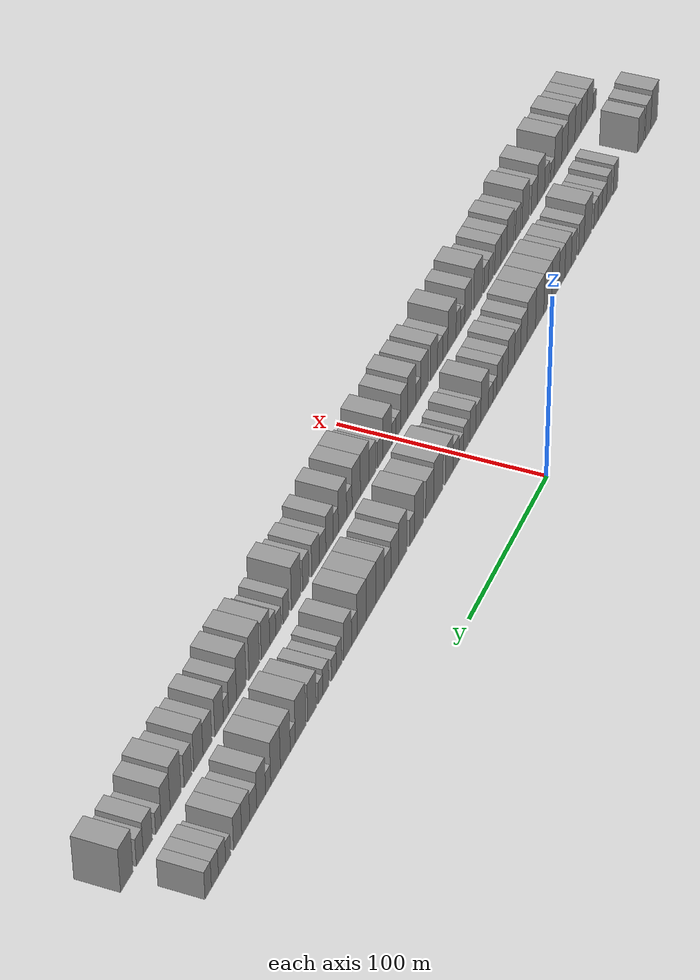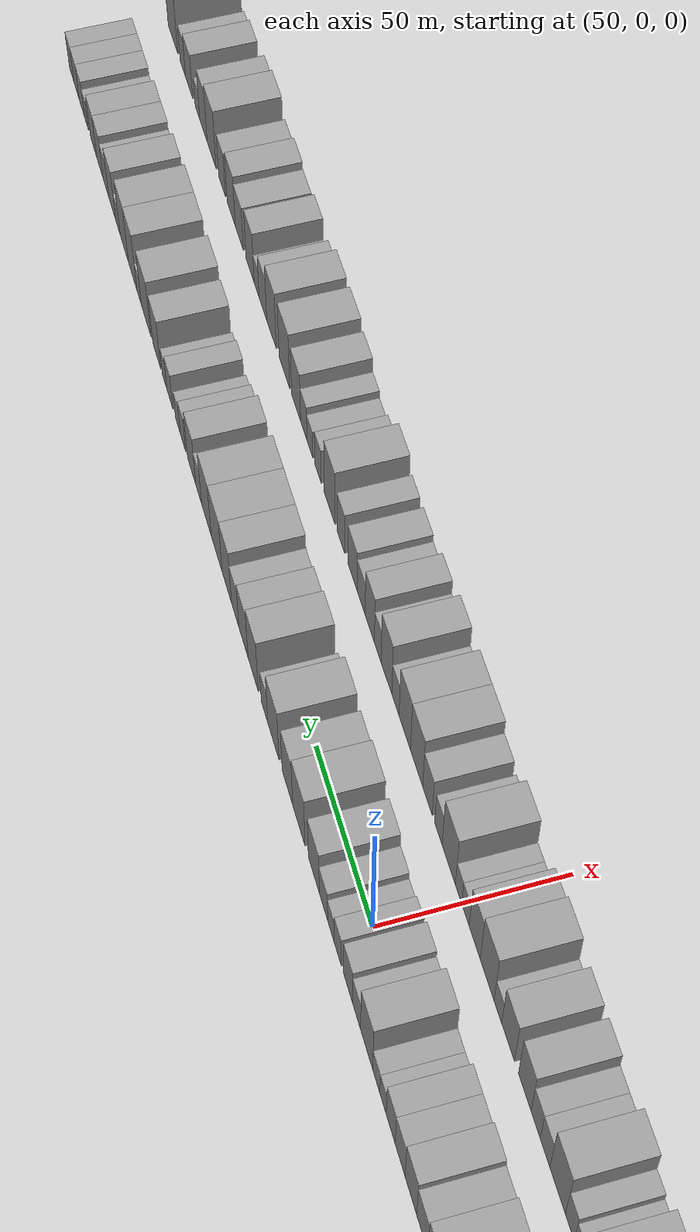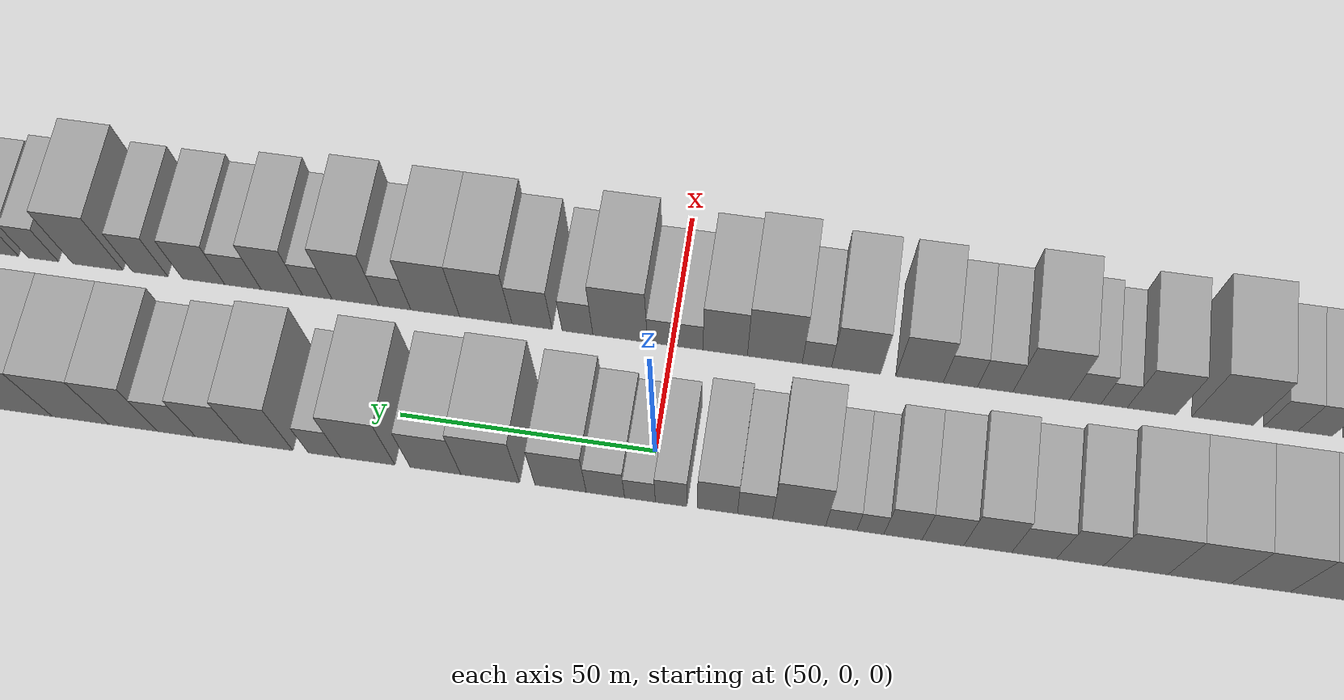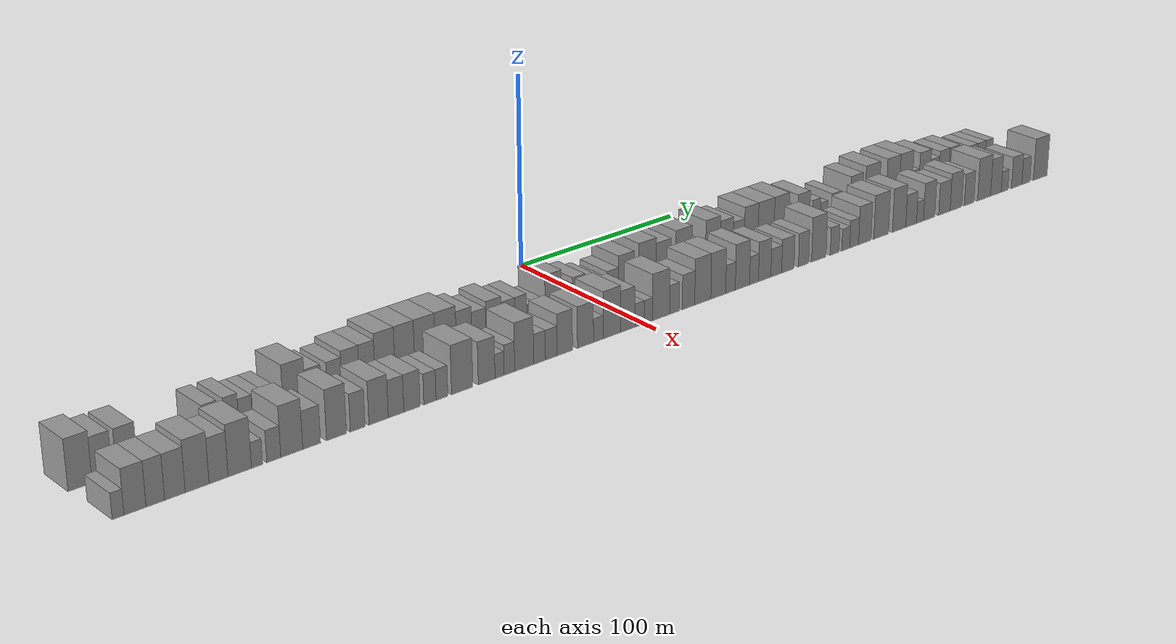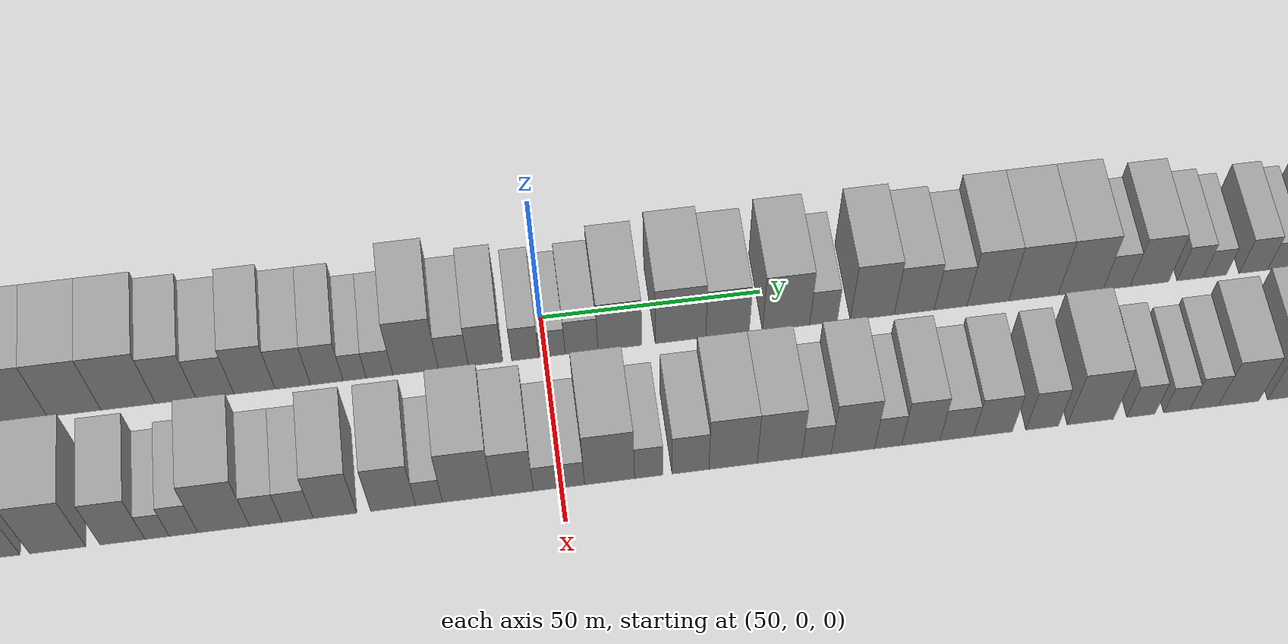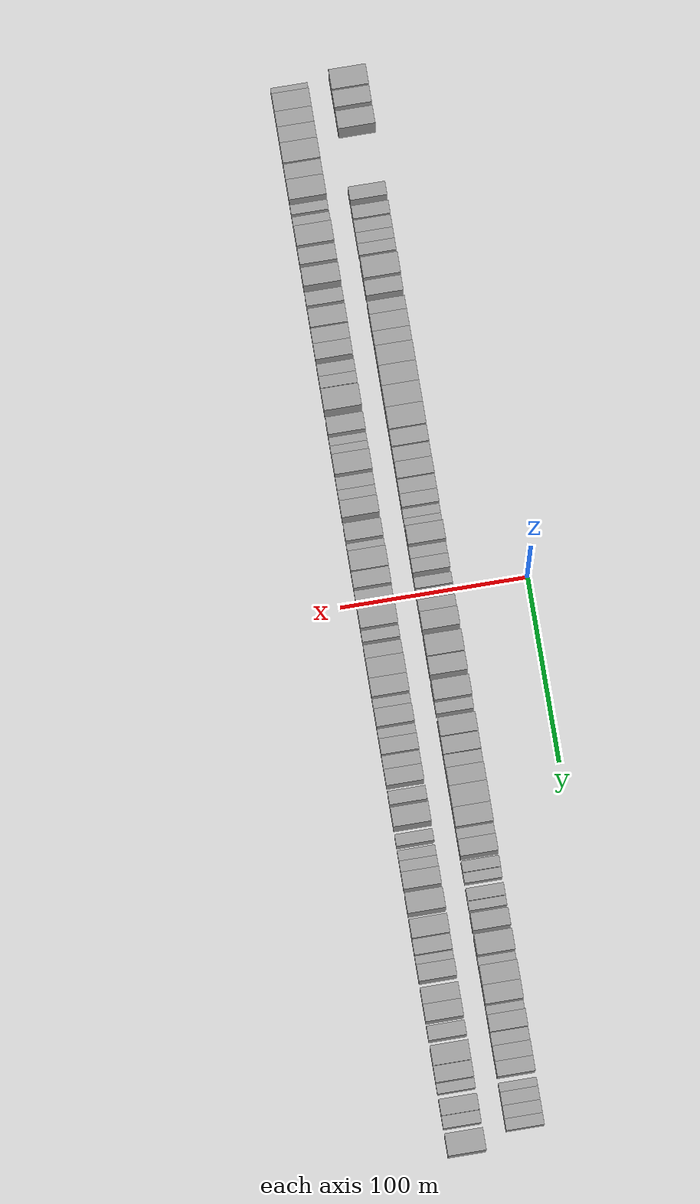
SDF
<sdf version="1.6">
 <world name="default">
  <scene>
   <sky><clouds><speed>12</speed></clouds></sky>
   <ambient>0.4 0.4 0.4 1</ambient>
   <background>0.7 0.7 0.7 1</background>
   <shadows>1</shadows>
  </scene>
  <gravity>0 0 -9.8066</gravity>
  <magnetic_field>6e-06 2.3e-05 -4.2e-05</magnetic_field>
  <physics default="0" name="default_physics" type="ode">
   <ode>
    <solver>
     <type>quick</type>
     <iters>10</iters>
     <sor>1.0</sor>
     <use_dynamic_moi_rescaling>0</use_dynamic_moi_rescaling>
    </solver>
    <constraints>
     <cfm>0</cfm>
     <erp>0.2</erp>
     <contact_max_correcting_vel>100</contact_max_correcting_vel>
     <contact_surface_layer>0.001</contact_surface_layer>
    </constraints>
   </ode>
   <max_step_size>0.004</max_step_size>
   <real_time_factor>1</real_time_factor>
   <real_time_update_rate>250</real_time_update_rate>
  </physics>
  <light name="sun" type="directional">
   <pose>0 0 10 0 0 0</pose>
   <diffuse>0.8 0.8 0.8 1</diffuse>
   <specular>0.2 0.2 0.2 1</specular>
   <attenuation>
    <range>1000</range>
    <constant>0.9</constant>
    <linear>0.01</linear>
    <quadratic>0.001</quadratic>
   </attenuation>
   <direction>-0.5 0.1 -0.9</direction>
  </light>
  <model name="building_1">
   <static>1</static>
   <pose>50.0000 -278.4930 0 0.000000 0.000000 0.000000</pose>
   <link name="link">
    <pose>0 0 12.00 0 0 0</pose>
    <collision name="collision"><geometry><box><size>20.0000 11.0139 24.0000</size></box></geometry></collision>
    <visual name="visual">
     <cast_shadows>0</cast_shadows>
     <geometry><box><size>20.0000 11.0139 24.0000</size></box></geometry>
     <material>
      <script>
       <uri>model://grey_wall/materials/scripts</uri>
       <uri>model://grey_wall/materials/textures</uri>
       <name>vrc/grey_wall</name>
      </script>
     </material>
    </visual>
   </link>
  </model>
  <model name="building_2">
   <static>1</static>
   <pose>50.0000 -268.3517 0 0.000000 0.000000 0.000000</pose>
   <link name="link">
    <pose>0 0 10.50 0 0 0</pose>
    <collision name="collision"><geometry><box><size>20.0000 9.2688 21.0000</size></box></geometry></collision>
    <visual name="visual">
     <cast_shadows>0</cast_shadows>
     <geometry><box><size>20.0000 9.2688 21.0000</size></box></geometry>
     <material>
      <script>
       <uri>model://grey_wall/materials/scripts</uri>
       <uri>model://grey_wall/materials/textures</uri>
       <name>vrc/grey_wall</name>
      </script>
     </material>
    </visual>
   </link>
  </model>
  <model name="building_3">
   <static>1</static>
   <pose>50.0000 -256.8036 0 0.000000 0.000000 0.000000</pose>
   <link name="link">
    <pose>0 0 10.50 0 0 0</pose>
    <collision name="collision"><geometry><box><size>20.0000 9.8273 21.0000</size></box></geometry></collision>
    <visual name="visual">
     <cast_shadows>0</cast_shadows>
     <geometry><box><size>20.0000 9.8273 21.0000</size></box></geometry>
     <material>
      <script>
       <uri>model://grey_wall/materials/scripts</uri>
       <uri>model://grey_wall/materials/textures</uri>
       <name>vrc/grey_wall</name>
      </script>
     </material>
    </visual>
   </link>
  </model>
  <model name="building_4">
   <static>1</static>
   <pose>50.0000 -216.7169 0 0.000000 0.000000 0.000000</pose>
   <link name="link">
    <pose>0 0 9.00 0 0 0</pose>
    <collision name="collision"><geometry><box><size>20.0000 7.4487 18.0000</size></box></geometry></collision>
    <visual name="visual">
     <cast_shadows>0</cast_shadows>
     <geometry><box><size>20.0000 7.4487 18.0000</size></box></geometry>
     <material>
      <script>
       <uri>model://grey_wall/materials/scripts</uri>
       <uri>model://grey_wall/materials/textures</uri>
       <name>vrc/grey_wall</name>
      </script>
     </material>
    </visual>
   </link>
  </model>
  <model name="building_5">
   <static>1</static>
   <pose>50.0000 -206.3585 0 0.000000 0.000000 0.000000</pose>
   <link name="link">
    <pose>0 0 9.00 0 0 0</pose>
    <collision name="collision"><geometry><box><size>20.0000 7.2680 18.0000</size></box></geometry></collision>
    <visual name="visual">
     <cast_shadows>0</cast_shadows>
     <geometry><box><size>20.0000 7.2680 18.0000</size></box></geometry>
     <material>
      <script>
       <uri>model://grey_wall/materials/scripts</uri>
       <uri>model://grey_wall/materials/textures</uri>
       <name>vrc/grey_wall</name>
      </script>
     </material>
    </visual>
   </link>
  </model>
  <model name="building_6">
   <static>1</static>
   <pose>50.0000 -199.2980 0 0.000000 0.000000 0.000000</pose>
   <link name="link">
    <pose>0 0 7.50 0 0 0</pose>
    <collision name="collision"><geometry><box><size>20.0000 6.8530 15.0000</size></box></geometry></collision>
    <visual name="visual">
     <cast_shadows>0</cast_shadows>
     <geometry><box><size>20.0000 6.8530 15.0000</size></box></geometry>
     <material>
      <script>
       <uri>model://grey_wall/materials/scripts</uri>
       <uri>model://grey_wall/materials/textures</uri>
       <name>vrc/grey_wall</name>
      </script>
     </material>
    </visual>
   </link>
  </model>
  <model name="building_7">
   <static>1</static>
   <pose>50.0000 -192.8294 0 0.000000 0.000000 0.000000</pose>
   <link name="link">
    <pose>0 0 7.50 0 0 0</pose>
    <collision name="collision"><geometry><box><size>20.0000 6.0842 15.0000</size></box></geometry></collision>
    <visual name="visual">
     <cast_shadows>0</cast_shadows>
     <geometry><box><size>20.0000 6.0842 15.0000</size></box></geometry>
     <material>
      <script>
       <uri>model://grey_wall/materials/scripts</uri>
       <uri>model://grey_wall/materials/textures</uri>
       <name>vrc/grey_wall</name>
      </script>
     </material>
    </visual>
   </link>
  </model>
  <model name="building_8">
   <static>1</static>
   <pose>50.0000 -186.5375 0 0.000000 0.000000 0.000000</pose>
   <link name="link">
    <pose>0 0 7.50 0 0 0</pose>
    <collision name="collision"><geometry><box><size>20.0000 6.4996 15.0000</size></box></geometry></collision>
    <visual name="visual">
     <cast_shadows>0</cast_shadows>
     <geometry><box><size>20.0000 6.4996 15.0000</size></box></geometry>
     <material>
      <script>
       <uri>model://grey_wall/materials/scripts</uri>
       <uri>model://grey_wall/materials/textures</uri>
       <name>vrc/grey_wall</name>
      </script>
     </material>
    </visual>
   </link>
  </model>
  <model name="building_9">
   <static>1</static>
   <pose>50.0000 -174.5439 0 0.000000 0.000000 0.000000</pose>
   <link name="link">
    <pose>0 0 12.00 0 0 0</pose>
    <collision name="collision"><geometry><box><size>20.0000 11.4876 24.0000</size></box></geometry></collision>
    <visual name="visual">
     <cast_shadows>0</cast_shadows>
     <geometry><box><size>20.0000 11.4876 24.0000</size></box></geometry>
     <material>
      <script>
       <uri>model://grey_wall/materials/scripts</uri>
       <uri>model://grey_wall/materials/textures</uri>
       <name>vrc/grey_wall</name>
      </script>
     </material>
    </visual>
   </link>
  </model>
  <model name="building_10">
   <static>1</static>
   <pose>50.0000 -164.6084 0 0.000000 0.000000 0.000000</pose>
   <link name="link">
    <pose>0 0 9.00 0 0 0</pose>
    <collision name="collision"><geometry><box><size>20.0000 8.3834 18.0000</size></box></geometry></collision>
    <visual name="visual">
     <cast_shadows>0</cast_shadows>
     <geometry><box><size>20.0000 8.3834 18.0000</size></box></geometry>
     <material>
      <script>
       <uri>model://grey_wall/materials/scripts</uri>
       <uri>model://grey_wall/materials/textures</uri>
       <name>vrc/grey_wall</name>
      </script>
     </material>
    </visual>
   </link>
  </model>
  <model name="building_11">
   <static>1</static>
   <pose>50.0000 -153.5251 0 0.000000 0.000000 0.000000</pose>
   <link name="link">
    <pose>0 0 9.00 0 0 0</pose>
    <collision name="collision"><geometry><box><size>20.0000 7.7832 18.0000</size></box></geometry></collision>
    <visual name="visual">
     <cast_shadows>0</cast_shadows>
     <geometry><box><size>20.0000 7.7832 18.0000</size></box></geometry>
     <material>
      <script>
       <uri>model://grey_wall/materials/scripts</uri>
       <uri>model://grey_wall/materials/textures</uri>
       <name>vrc/grey_wall</name>
      </script>
     </material>
    </visual>
   </link>
  </model>
  <model name="building_12">
   <static>1</static>
   <pose>50.0000 -144.9641 0 0.000000 0.000000 0.000000</pose>
   <link name="link">
    <pose>0 0 10.50 0 0 0</pose>
    <collision name="collision"><geometry><box><size>20.0000 9.3388 21.0000</size></box></geometry></collision>
    <visual name="visual">
     <cast_shadows>0</cast_shadows>
     <geometry><box><size>20.0000 9.3388 21.0000</size></box></geometry>
     <material>
      <script>
       <uri>model://grey_wall/materials/scripts</uri>
       <uri>model://grey_wall/materials/textures</uri>
       <name>vrc/grey_wall</name>
      </script>
     </material>
    </visual>
   </link>
  </model>
  <model name="building_13">
   <static>1</static>
   <pose>50.0000 -136.0853 0 0.000000 0.000000 0.000000</pose>
   <link name="link">
    <pose>0 0 10.50 0 0 0</pose>
    <collision name="collision"><geometry><box><size>20.0000 8.4189 21.0000</size></box></geometry></collision>
    <visual name="visual">
     <cast_shadows>0</cast_shadows>
     <geometry><box><size>20.0000 8.4189 21.0000</size></box></geometry>
     <material>
      <script>
       <uri>model://grey_wall/materials/scripts</uri>
       <uri>model://grey_wall/materials/textures</uri>
       <name>vrc/grey_wall</name>
      </script>
     </material>
    </visual>
   </link>
  </model>
  <model name="building_14">
   <static>1</static>
   <pose>50.0000 -126.4248 0 0.000000 0.000000 0.000000</pose>
   <link name="link">
    <pose>0 0 12.00 0 0 0</pose>
    <collision name="collision"><geometry><box><size>20.0000 10.9022 24.0000</size></box></geometry></collision>
    <visual name="visual">
     <cast_shadows>0</cast_shadows>
     <geometry><box><size>20.0000 10.9022 24.0000</size></box></geometry>
     <material>
      <script>
       <uri>model://grey_wall/materials/scripts</uri>
       <uri>model://grey_wall/materials/textures</uri>
       <name>vrc/grey_wall</name>
      </script>
     </material>
    </visual>
   </link>
  </model>
  <model name="building_15">
   <static>1</static>
   <pose>50.0000 -115.5003 0 0.000000 0.000000 0.000000</pose>
   <link name="link">
    <pose>0 0 12.00 0 0 0</pose>
    <collision name="collision"><geometry><box><size>20.0000 10.9469 24.0000</size></box></geometry></collision>
    <visual name="visual">
     <cast_shadows>0</cast_shadows>
     <geometry><box><size>20.0000 10.9469 24.0000</size></box></geometry>
     <material>
      <script>
       <uri>model://grey_wall/materials/scripts</uri>
       <uri>model://grey_wall/materials/textures</uri>
       <name>vrc/grey_wall</name>
      </script>
     </material>
    </visual>
   </link>
  </model>
  <model name="building_16">
   <static>1</static>
   <pose>50.0000 -104.1812 0 0.000000 0.000000 0.000000</pose>
   <link name="link">
    <pose>0 0 12.00 0 0 0</pose>
    <collision name="collision"><geometry><box><size>20.0000 11.6913 24.0000</size></box></geometry></collision>
    <visual name="visual">
     <cast_shadows>0</cast_shadows>
     <geometry><box><size>20.0000 11.6913 24.0000</size></box></geometry>
     <material>
      <script>
       <uri>model://grey_wall/materials/scripts</uri>
       <uri>model://grey_wall/materials/textures</uri>
       <name>vrc/grey_wall</name>
      </script>
     </material>
    </visual>
   </link>
  </model>
  <model name="building_17">
   <static>1</static>
   <pose>50.0000 -92.3757 0 0.000000 0.000000 0.000000</pose>
   <link name="link">
    <pose>0 0 12.00 0 0 0</pose>
    <collision name="collision"><geometry><box><size>20.0000 11.9197 24.0000</size></box></geometry></collision>
    <visual name="visual">
     <cast_shadows>0</cast_shadows>
     <geometry><box><size>20.0000 11.9197 24.0000</size></box></geometry>
     <material>
      <script>
       <uri>model://grey_wall/materials/scripts</uri>
       <uri>model://grey_wall/materials/textures</uri>
       <name>vrc/grey_wall</name>
      </script>
     </material>
    </visual>
   </link>
  </model>
  <model name="building_18">
   <static>1</static>
   <pose>50.0000 -81.9634 0 0.000000 0.000000 0.000000</pose>
   <link name="link">
    <pose>0 0 10.50 0 0 0</pose>
    <collision name="collision"><geometry><box><size>20.0000 8.9050 21.0000</size></box></geometry></collision>
    <visual name="visual">
     <cast_shadows>0</cast_shadows>
     <geometry><box><size>20.0000 8.9050 21.0000</size></box></geometry>
     <material>
      <script>
       <uri>model://grey_wall/materials/scripts</uri>
       <uri>model://grey_wall/materials/textures</uri>
       <name>vrc/grey_wall</name>
      </script>
     </material>
    </visual>
   </link>
  </model>
  <model name="building_19">
   <static>1</static>
   <pose>50.0000 -73.3345 0 0.000000 0.000000 0.000000</pose>
   <link name="link">
    <pose>0 0 9.00 0 0 0</pose>
    <collision name="collision"><geometry><box><size>20.0000 8.3528 18.0000</size></box></geometry></collision>
    <visual name="visual">
     <cast_shadows>0</cast_shadows>
     <geometry><box><size>20.0000 8.3528 18.0000</size></box></geometry>
     <material>
      <script>
       <uri>model://grey_wall/materials/scripts</uri>
       <uri>model://grey_wall/materials/textures</uri>
       <name>vrc/grey_wall</name>
      </script>
     </material>
    </visual>
   </link>
  </model>
  <model name="building_20">
   <static>1</static>
   <pose>50.0000 -64.6351 0 0.000000 0.000000 0.000000</pose>
   <link name="link">
    <pose>0 0 10.50 0 0 0</pose>
    <collision name="collision"><geometry><box><size>20.0000 9.0460 21.0000</size></box></geometry></collision>
    <visual name="visual">
     <cast_shadows>0</cast_shadows>
     <geometry><box><size>20.0000 9.0460 21.0000</size></box></geometry>
     <material>
      <script>
       <uri>model://grey_wall/materials/scripts</uri>
       <uri>model://grey_wall/materials/textures</uri>
       <name>vrc/grey_wall</name>
      </script>
     </material>
    </visual>
   </link>
  </model>
  <model name="building_21">
   <static>1</static>
   <pose>50.0000 -56.1918 0 0.000000 0.000000 0.000000</pose>
   <link name="link">
    <pose>0 0 9.00 0 0 0</pose>
    <collision name="collision"><geometry><box><size>20.0000 7.8406 18.0000</size></box></geometry></collision>
    <visual name="visual">
     <cast_shadows>0</cast_shadows>
     <geometry><box><size>20.0000 7.8406 18.0000</size></box></geometry>
     <material>
      <script>
       <uri>model://grey_wall/materials/scripts</uri>
       <uri>model://grey_wall/materials/textures</uri>
       <name>vrc/grey_wall</name>
      </script>
     </material>
    </visual>
   </link>
  </model>
  <model name="building_22">
   <static>1</static>
   <pose>50.0000 -48.6585 0 0.000000 0.000000 0.000000</pose>
   <link name="link">
    <pose>0 0 9.00 0 0 0</pose>
    <collision name="collision"><geometry><box><size>20.0000 7.2261 18.0000</size></box></geometry></collision>
    <visual name="visual">
     <cast_shadows>0</cast_shadows>
     <geometry><box><size>20.0000 7.2261 18.0000</size></box></geometry>
     <material>
      <script>
       <uri>model://grey_wall/materials/scripts</uri>
       <uri>model://grey_wall/materials/textures</uri>
       <name>vrc/grey_wall</name>
      </script>
     </material>
    </visual>
   </link>
  </model>
  <model name="building_23">
   <static>1</static>
   <pose>50.0000 -42.4910 0 0.000000 0.000000 0.000000</pose>
   <link name="link">
    <pose>0 0 6.00 0 0 0</pose>
    <collision name="collision"><geometry><box><size>20.0000 5.1089 12.0000</size></box></geometry></collision>
    <visual name="visual">
     <cast_shadows>0</cast_shadows>
     <geometry><box><size>20.0000 5.1089 12.0000</size></box></geometry>
     <material>
      <script>
       <uri>model://grey_wall/materials/scripts</uri>
       <uri>model://grey_wall/materials/textures</uri>
       <name>vrc/grey_wall</name>
      </script>
     </material>
    </visual>
   </link>
  </model>
  <model name="building_24">
   <static>1</static>
   <pose>50.0000 -36.9791 0 0.000000 0.000000 0.000000</pose>
   <link name="link">
    <pose>0 0 6.00 0 0 0</pose>
    <collision name="collision"><geometry><box><size>20.0000 5.9149 12.0000</size></box></geometry></collision>
    <visual name="visual">
     <cast_shadows>0</cast_shadows>
     <geometry><box><size>20.0000 5.9149 12.0000</size></box></geometry>
     <material>
      <script>
       <uri>model://grey_wall/materials/scripts</uri>
       <uri>model://grey_wall/materials/textures</uri>
       <name>vrc/grey_wall</name>
      </script>
     </material>
    </visual>
   </link>
  </model>
  <model name="building_25">
   <static>1</static>
   <pose>50.0000 -28.9703 0 0.000000 0.000000 0.000000</pose>
   <link name="link">
    <pose>0 0 12.00 0 0 0</pose>
    <collision name="collision"><geometry><box><size>20.0000 10.1026 24.0000</size></box></geometry></collision>
    <visual name="visual">
     <cast_shadows>0</cast_shadows>
     <geometry><box><size>20.0000 10.1026 24.0000</size></box></geometry>
     <material>
      <script>
       <uri>model://grey_wall/materials/scripts</uri>
       <uri>model://grey_wall/materials/textures</uri>
       <name>vrc/grey_wall</name>
      </script>
     </material>
    </visual>
   </link>
  </model>
  <model name="building_26">
   <static>1</static>
   <pose>50.0000 -20.5697 0 0.000000 0.000000 0.000000</pose>
   <link name="link">
    <pose>0 0 7.50 0 0 0</pose>
    <collision name="collision"><geometry><box><size>20.0000 6.6987 15.0000</size></box></geometry></collision>
    <visual name="visual">
     <cast_shadows>0</cast_shadows>
     <geometry><box><size>20.0000 6.6987 15.0000</size></box></geometry>
     <material>
      <script>
       <uri>model://grey_wall/materials/scripts</uri>
       <uri>model://grey_wall/materials/textures</uri>
       <name>vrc/grey_wall</name>
      </script>
     </material>
    </visual>
   </link>
  </model>
  <model name="building_27">
   <static>1</static>
   <pose>50.0000 -13.3778 0 0.000000 0.000000 0.000000</pose>
   <link name="link">
    <pose>0 0 9.00 0 0 0</pose>
    <collision name="collision"><geometry><box><size>20.0000 7.6851 18.0000</size></box></geometry></collision>
    <visual name="visual">
     <cast_shadows>0</cast_shadows>
     <geometry><box><size>20.0000 7.6851 18.0000</size></box></geometry>
     <material>
      <script>
       <uri>model://grey_wall/materials/scripts</uri>
       <uri>model://grey_wall/materials/textures</uri>
       <name>vrc/grey_wall</name>
      </script>
     </material>
    </visual>
   </link>
  </model>
  <model name="building_28">
   <static>1</static>
   <pose>50.0000 -4.5084 0 0.000000 0.000000 0.000000</pose>
   <link name="link">
    <pose>0 0 7.50 0 0 0</pose>
    <collision name="collision"><geometry><box><size>20.0000 6.0537 15.0000</size></box></geometry></collision>
    <visual name="visual">
     <cast_shadows>0</cast_shadows>
     <geometry><box><size>20.0000 6.0537 15.0000</size></box></geometry>
     <material>
      <script>
       <uri>model://grey_wall/materials/scripts</uri>
       <uri>model://grey_wall/materials/textures</uri>
       <name>vrc/grey_wall</name>
      </script>
     </material>
    </visual>
   </link>
  </model>
  <model name="building_29">
   <static>1</static>
   <pose>50.0000 1.4817 0 0.000000 0.000000 0.000000</pose>
   <link name="link">
    <pose>0 0 6.00 0 0 0</pose>
    <collision name="collision"><geometry><box><size>20.0000 5.9267 12.0000</size></box></geometry></collision>
    <visual name="visual">
     <cast_shadows>0</cast_shadows>
     <geometry><box><size>20.0000 5.9267 12.0000</size></box></geometry>
     <material>
      <script>
       <uri>model://grey_wall/materials/scripts</uri>
       <uri>model://grey_wall/materials/textures</uri>
       <name>vrc/grey_wall</name>
      </script>
     </material>
    </visual>
   </link>
  </model>
  <model name="building_30">
   <static>1</static>
   <pose>50.0000 8.1328 0 0.000000 0.000000 0.000000</pose>
   <link name="link">
    <pose>0 0 7.50 0 0 0</pose>
    <collision name="collision"><geometry><box><size>20.0000 7.3756 15.0000</size></box></geometry></collision>
    <visual name="visual">
     <cast_shadows>0</cast_shadows>
     <geometry><box><size>20.0000 7.3756 15.0000</size></box></geometry>
     <material>
      <script>
       <uri>model://grey_wall/materials/scripts</uri>
       <uri>model://grey_wall/materials/textures</uri>
       <name>vrc/grey_wall</name>
      </script>
     </material>
    </visual>
   </link>
  </model>
  <model name="building_31">
   <static>1</static>
   <pose>50.0000 16.7723 0 0.000000 0.000000 0.000000</pose>
   <link name="link">
    <pose>0 0 10.50 0 0 0</pose>
    <collision name="collision"><geometry><box><size>20.0000 9.9033 21.0000</size></box></geometry></collision>
    <visual name="visual">
     <cast_shadows>0</cast_shadows>
     <geometry><box><size>20.0000 9.9033 21.0000</size></box></geometry>
     <material>
      <script>
       <uri>model://grey_wall/materials/scripts</uri>
       <uri>model://grey_wall/materials/textures</uri>
       <name>vrc/grey_wall</name>
      </script>
     </material>
    </visual>
   </link>
  </model>
  <model name="building_32">
   <static>1</static>
   <pose>50.0000 30.4309 0 0.000000 0.000000 0.000000</pose>
   <link name="link">
    <pose>0 0 12.00 0 0 0</pose>
    <collision name="collision"><geometry><box><size>20.0000 11.4141 24.0000</size></box></geometry></collision>
    <visual name="visual">
     <cast_shadows>0</cast_shadows>
     <geometry><box><size>20.0000 11.4141 24.0000</size></box></geometry>
     <material>
      <script>
       <uri>model://grey_wall/materials/scripts</uri>
       <uri>model://grey_wall/materials/textures</uri>
       <name>vrc/grey_wall</name>
      </script>
     </material>
    </visual>
   </link>
  </model>
  <model name="building_33">
   <static>1</static>
   <pose>50.0000 41.0678 0 0.000000 0.000000 0.000000</pose>
   <link name="link">
    <pose>0 0 10.50 0 0 0</pose>
    <collision name="collision"><geometry><box><size>20.0000 9.8596 21.0000</size></box></geometry></collision>
    <visual name="visual">
     <cast_shadows>0</cast_shadows>
     <geometry><box><size>20.0000 9.8596 21.0000</size></box></geometry>
     <material>
      <script>
       <uri>model://grey_wall/materials/scripts</uri>
       <uri>model://grey_wall/materials/textures</uri>
       <name>vrc/grey_wall</name>
      </script>
     </material>
    </visual>
   </link>
  </model>
  <model name="building_34">
   <static>1</static>
   <pose>50.0000 54.3550 0 0.000000 0.000000 0.000000</pose>
   <link name="link">
    <pose>0 0 12.00 0 0 0</pose>
    <collision name="collision"><geometry><box><size>20.0000 10.7149 24.0000</size></box></geometry></collision>
    <visual name="visual">
     <cast_shadows>0</cast_shadows>
     <geometry><box><size>20.0000 10.7149 24.0000</size></box></geometry>
     <material>
      <script>
       <uri>model://grey_wall/materials/scripts</uri>
       <uri>model://grey_wall/materials/textures</uri>
       <name>vrc/grey_wall</name>
      </script>
     </material>
    </visual>
   </link>
  </model>
  <model name="building_35">
   <static>1</static>
   <pose>50.0000 62.8601 0 0.000000 0.000000 0.000000</pose>
   <link name="link">
    <pose>0 0 7.50 0 0 0</pose>
    <collision name="collision"><geometry><box><size>20.0000 6.2953 15.0000</size></box></geometry></collision>
    <visual name="visual">
     <cast_shadows>0</cast_shadows>
     <geometry><box><size>20.0000 6.2953 15.0000</size></box></geometry>
     <material>
      <script>
       <uri>model://grey_wall/materials/scripts</uri>
       <uri>model://grey_wall/materials/textures</uri>
       <name>vrc/grey_wall</name>
      </script>
     </material>
    </visual>
   </link>
  </model>
  <model name="building_36">
   <static>1</static>
   <pose>50.0000 74.0234 0 0.000000 0.000000 0.000000</pose>
   <link name="link">
    <pose>0 0 12.00 0 0 0</pose>
    <collision name="collision"><geometry><box><size>20.0000 10.0312 24.0000</size></box></geometry></collision>
    <visual name="visual">
     <cast_shadows>0</cast_shadows>
     <geometry><box><size>20.0000 10.0312 24.0000</size></box></geometry>
     <material>
      <script>
       <uri>model://grey_wall/materials/scripts</uri>
       <uri>model://grey_wall/materials/textures</uri>
       <name>vrc/grey_wall</name>
      </script>
     </material>
    </visual>
   </link>
  </model>
  <model name="building_37">
   <static>1</static>
   <pose>50.0000 83.6397 0 0.000000 0.000000 0.000000</pose>
   <link name="link">
    <pose>0 0 10.50 0 0 0</pose>
    <collision name="collision"><geometry><box><size>20.0000 9.2015 21.0000</size></box></geometry></collision>
    <visual name="visual">
     <cast_shadows>0</cast_shadows>
     <geometry><box><size>20.0000 9.2015 21.0000</size></box></geometry>
     <material>
      <script>
       <uri>model://grey_wall/materials/scripts</uri>
       <uri>model://grey_wall/materials/textures</uri>
       <name>vrc/grey_wall</name>
      </script>
     </material>
    </visual>
   </link>
  </model>
  <model name="building_38">
   <static>1</static>
   <pose>50.0000 92.0039 0 0.000000 0.000000 0.000000</pose>
   <link name="link">
    <pose>0 0 9.00 0 0 0</pose>
    <collision name="collision"><geometry><box><size>20.0000 7.5267 18.0000</size></box></geometry></collision>
    <visual name="visual">
     <cast_shadows>0</cast_shadows>
     <geometry><box><size>20.0000 7.5267 18.0000</size></box></geometry>
     <material>
      <script>
       <uri>model://grey_wall/materials/scripts</uri>
       <uri>model://grey_wall/materials/textures</uri>
       <name>vrc/grey_wall</name>
      </script>
     </material>
    </visual>
   </link>
  </model>
  <model name="building_39">
   <static>1</static>
   <pose>50.0000 100.5890 0 0.000000 0.000000 0.000000</pose>
   <link name="link">
    <pose>0 0 12.00 0 0 0</pose>
    <collision name="collision"><geometry><box><size>20.0000 9.6436 24.0000</size></box></geometry></collision>
    <visual name="visual">
     <cast_shadows>0</cast_shadows>
     <geometry><box><size>20.0000 9.6436 24.0000</size></box></geometry>
     <material>
      <script>
       <uri>model://grey_wall/materials/scripts</uri>
       <uri>model://grey_wall/materials/textures</uri>
       <name>vrc/grey_wall</name>
      </script>
     </material>
    </visual>
   </link>
  </model>
  <model name="building_40">
   <static>1</static>
   <pose>50.0000 111.1085 0 0.000000 0.000000 0.000000</pose>
   <link name="link">
    <pose>0 0 12.00 0 0 0</pose>
    <collision name="collision"><geometry><box><size>20.0000 11.3954 24.0000</size></box></geometry></collision>
    <visual name="visual">
     <cast_shadows>0</cast_shadows>
     <geometry><box><size>20.0000 11.3954 24.0000</size></box></geometry>
     <material>
      <script>
       <uri>model://grey_wall/materials/scripts</uri>
       <uri>model://grey_wall/materials/textures</uri>
       <name>vrc/grey_wall</name>
      </script>
     </material>
    </visual>
   </link>
  </model>
  <model name="building_41">
   <static>1</static>
   <pose>50.0000 122.0105 0 0.000000 0.000000 0.000000</pose>
   <link name="link">
    <pose>0 0 12.00 0 0 0</pose>
    <collision name="collision"><geometry><box><size>20.0000 10.4088 24.0000</size></box></geometry></collision>
    <visual name="visual">
     <cast_shadows>0</cast_shadows>
     <geometry><box><size>20.0000 10.4088 24.0000</size></box></geometry>
     <material>
      <script>
       <uri>model://grey_wall/materials/scripts</uri>
       <uri>model://grey_wall/materials/textures</uri>
       <name>vrc/grey_wall</name>
      </script>
     </material>
    </visual>
   </link>
  </model>
  <model name="building_42">
   <static>1</static>
   <pose>50.0000 130.3506 0 0.000000 0.000000 0.000000</pose>
   <link name="link">
    <pose>0 0 7.50 0 0 0</pose>
    <collision name="collision"><geometry><box><size>20.0000 6.2713 15.0000</size></box></geometry></collision>
    <visual name="visual">
     <cast_shadows>0</cast_shadows>
     <geometry><box><size>20.0000 6.2713 15.0000</size></box></geometry>
     <material>
      <script>
       <uri>model://grey_wall/materials/scripts</uri>
       <uri>model://grey_wall/materials/textures</uri>
       <name>vrc/grey_wall</name>
      </script>
     </material>
    </visual>
   </link>
  </model>
  <model name="building_43">
   <static>1</static>
   <pose>50.0000 137.9851 0 0.000000 0.000000 0.000000</pose>
   <link name="link">
    <pose>0 0 10.50 0 0 0</pose>
    <collision name="collision"><geometry><box><size>20.0000 8.9977 21.0000</size></box></geometry></collision>
    <visual name="visual">
     <cast_shadows>0</cast_shadows>
     <geometry><box><size>20.0000 8.9977 21.0000</size></box></geometry>
     <material>
      <script>
       <uri>model://grey_wall/materials/scripts</uri>
       <uri>model://grey_wall/materials/textures</uri>
       <name>vrc/grey_wall</name>
      </script>
     </material>
    </visual>
   </link>
  </model>
  <model name="building_44">
   <static>1</static>
   <pose>50.0000 147.4959 0 0.000000 0.000000 0.000000</pose>
   <link name="link">
    <pose>0 0 7.50 0 0 0</pose>
    <collision name="collision"><geometry><box><size>20.0000 6.0239 15.0000</size></box></geometry></collision>
    <visual name="visual">
     <cast_shadows>0</cast_shadows>
     <geometry><box><size>20.0000 6.0239 15.0000</size></box></geometry>
     <material>
      <script>
       <uri>model://grey_wall/materials/scripts</uri>
       <uri>model://grey_wall/materials/textures</uri>
       <name>vrc/grey_wall</name>
      </script>
     </material>
    </visual>
   </link>
  </model>
  <model name="building_45">
   <static>1</static>
   <pose>50.0000 153.2212 0 0.000000 0.000000 0.000000</pose>
   <link name="link">
    <pose>0 0 6.00 0 0 0</pose>
    <collision name="collision"><geometry><box><size>20.0000 5.4267 12.0000</size></box></geometry></collision>
    <visual name="visual">
     <cast_shadows>0</cast_shadows>
     <geometry><box><size>20.0000 5.4267 12.0000</size></box></geometry>
     <material>
      <script>
       <uri>model://grey_wall/materials/scripts</uri>
       <uri>model://grey_wall/materials/textures</uri>
       <name>vrc/grey_wall</name>
      </script>
     </material>
    </visual>
   </link>
  </model>
  <model name="building_46">
   <static>1</static>
   <pose>50.0000 162.2560 0 0.000000 0.000000 0.000000</pose>
   <link name="link">
    <pose>0 0 7.50 0 0 0</pose>
    <collision name="collision"><geometry><box><size>20.0000 6.6430 15.0000</size></box></geometry></collision>
    <visual name="visual">
     <cast_shadows>0</cast_shadows>
     <geometry><box><size>20.0000 6.6430 15.0000</size></box></geometry>
     <material>
      <script>
       <uri>model://grey_wall/materials/scripts</uri>
       <uri>model://grey_wall/materials/textures</uri>
       <name>vrc/grey_wall</name>
      </script>
     </material>
    </visual>
   </link>
  </model>
  <model name="building_47">
   <static>1</static>
   <pose>50.0000 168.0989 0 0.000000 0.000000 0.000000</pose>
   <link name="link">
    <pose>0 0 6.00 0 0 0</pose>
    <collision name="collision"><geometry><box><size>20.0000 5.0428 12.0000</size></box></geometry></collision>
    <visual name="visual">
     <cast_shadows>0</cast_shadows>
     <geometry><box><size>20.0000 5.0428 12.0000</size></box></geometry>
     <material>
      <script>
       <uri>model://grey_wall/materials/scripts</uri>
       <uri>model://grey_wall/materials/textures</uri>
       <name>vrc/grey_wall</name>
      </script>
     </material>
    </visual>
   </link>
  </model>
  <model name="building_48">
   <static>1</static>
   <pose>50.0000 177.2669 0 0.000000 0.000000 0.000000</pose>
   <link name="link">
    <pose>0 0 10.50 0 0 0</pose>
    <collision name="collision"><geometry><box><size>20.0000 9.2932 21.0000</size></box></geometry></collision>
    <visual name="visual">
     <cast_shadows>0</cast_shadows>
     <geometry><box><size>20.0000 9.2932 21.0000</size></box></geometry>
     <material>
      <script>
       <uri>model://grey_wall/materials/scripts</uri>
       <uri>model://grey_wall/materials/textures</uri>
       <name>vrc/grey_wall</name>
      </script>
     </material>
    </visual>
   </link>
  </model>
  <model name="building_49">
   <static>1</static>
   <pose>50.0000 189.5027 0 0.000000 0.000000 0.000000</pose>
   <link name="link">
    <pose>0 0 12.00 0 0 0</pose>
    <collision name="collision"><geometry><box><size>20.0000 11.1784 24.0000</size></box></geometry></collision>
    <visual name="visual">
     <cast_shadows>0</cast_shadows>
     <geometry><box><size>20.0000 11.1784 24.0000</size></box></geometry>
     <material>
      <script>
       <uri>model://grey_wall/materials/scripts</uri>
       <uri>model://grey_wall/materials/textures</uri>
       <name>vrc/grey_wall</name>
      </script>
     </material>
    </visual>
   </link>
  </model>
  <model name="building_50">
   <static>1</static>
   <pose>50.0000 197.7847 0 0.000000 0.000000 0.000000</pose>
   <link name="link">
    <pose>0 0 6.00 0 0 0</pose>
    <collision name="collision"><geometry><box><size>20.0000 5.3856 12.0000</size></box></geometry></collision>
    <visual name="visual">
     <cast_shadows>0</cast_shadows>
     <geometry><box><size>20.0000 5.3856 12.0000</size></box></geometry>
     <material>
      <script>
       <uri>model://grey_wall/materials/scripts</uri>
       <uri>model://grey_wall/materials/textures</uri>
       <name>vrc/grey_wall</name>
      </script>
     </material>
    </visual>
   </link>
  </model>
  <model name="building_51">
   <static>1</static>
   <pose>50.0000 205.6232 0 0.000000 0.000000 0.000000</pose>
   <link name="link">
    <pose>0 0 12.00 0 0 0</pose>
    <collision name="collision"><geometry><box><size>20.0000 10.2915 24.0000</size></box></geometry></collision>
    <visual name="visual">
     <cast_shadows>0</cast_shadows>
     <geometry><box><size>20.0000 10.2915 24.0000</size></box></geometry>
     <material>
      <script>
       <uri>model://grey_wall/materials/scripts</uri>
       <uri>model://grey_wall/materials/textures</uri>
       <name>vrc/grey_wall</name>
      </script>
     </material>
    </visual>
   </link>
  </model>
  <model name="building_52">
   <static>1</static>
   <pose>50.0000 215.8023 0 0.000000 0.000000 0.000000</pose>
   <link name="link">
    <pose>0 0 12.00 0 0 0</pose>
    <collision name="collision"><geometry><box><size>20.0000 10.0666 24.0000</size></box></geometry></collision>
    <visual name="visual">
     <cast_shadows>0</cast_shadows>
     <geometry><box><size>20.0000 10.0666 24.0000</size></box></geometry>
     <material>
      <script>
       <uri>model://grey_wall/materials/scripts</uri>
       <uri>model://grey_wall/materials/textures</uri>
       <name>vrc/grey_wall</name>
      </script>
     </material>
    </visual>
   </link>
  </model>
  <model name="building_53">
   <static>1</static>
   <pose>50.0000 223.4891 0 0.000000 0.000000 0.000000</pose>
   <link name="link">
    <pose>0 0 6.00 0 0 0</pose>
    <collision name="collision"><geometry><box><size>20.0000 5.3071 12.0000</size></box></geometry></collision>
    <visual name="visual">
     <cast_shadows>0</cast_shadows>
     <geometry><box><size>20.0000 5.3071 12.0000</size></box></geometry>
     <material>
      <script>
       <uri>model://grey_wall/materials/scripts</uri>
       <uri>model://grey_wall/materials/textures</uri>
       <name>vrc/grey_wall</name>
      </script>
     </material>
    </visual>
   </link>
  </model>
  <model name="building_54">
   <static>1</static>
   <pose>50.0000 230.6650 0 0.000000 0.000000 0.000000</pose>
   <link name="link">
    <pose>0 0 10.50 0 0 0</pose>
    <collision name="collision"><geometry><box><size>20.0000 9.0448 21.0000</size></box></geometry></collision>
    <visual name="visual">
     <cast_shadows>0</cast_shadows>
     <geometry><box><size>20.0000 9.0448 21.0000</size></box></geometry>
     <material>
      <script>
       <uri>model://grey_wall/materials/scripts</uri>
       <uri>model://grey_wall/materials/textures</uri>
       <name>vrc/grey_wall</name>
      </script>
     </material>
    </visual>
   </link>
  </model>
  <model name="building_55">
   <static>1</static>
   <pose>50.0000 238.7319 0 0.000000 0.000000 0.000000</pose>
   <link name="link">
    <pose>0 0 7.50 0 0 0</pose>
    <collision name="collision"><geometry><box><size>20.0000 7.0890 15.0000</size></box></geometry></collision>
    <visual name="visual">
     <cast_shadows>0</cast_shadows>
     <geometry><box><size>20.0000 7.0890 15.0000</size></box></geometry>
     <material>
      <script>
       <uri>model://grey_wall/materials/scripts</uri>
       <uri>model://grey_wall/materials/textures</uri>
       <name>vrc/grey_wall</name>
      </script>
     </material>
    </visual>
   </link>
  </model>
  <model name="building_56">
   <static>1</static>
   <pose>50.0000 246.3394 0 0.000000 0.000000 0.000000</pose>
   <link name="link">
    <pose>0 0 9.00 0 0 0</pose>
    <collision name="collision"><geometry><box><size>20.0000 8.1259 18.0000</size></box></geometry></collision>
    <visual name="visual">
     <cast_shadows>0</cast_shadows>
     <geometry><box><size>20.0000 8.1259 18.0000</size></box></geometry>
     <material>
      <script>
       <uri>model://grey_wall/materials/scripts</uri>
       <uri>model://grey_wall/materials/textures</uri>
       <name>vrc/grey_wall</name>
      </script>
     </material>
    </visual>
   </link>
  </model>
  <model name="building_57">
   <static>1</static>
   <pose>50.0000 254.4463 0 0.000000 0.000000 0.000000</pose>
   <link name="link">
    <pose>0 0 9.00 0 0 0</pose>
    <collision name="collision"><geometry><box><size>20.0000 8.0880 18.0000</size></box></geometry></collision>
    <visual name="visual">
     <cast_shadows>0</cast_shadows>
     <geometry><box><size>20.0000 8.0880 18.0000</size></box></geometry>
     <material>
      <script>
       <uri>model://grey_wall/materials/scripts</uri>
       <uri>model://grey_wall/materials/textures</uri>
       <name>vrc/grey_wall</name>
      </script>
     </material>
    </visual>
   </link>
  </model>
  <model name="building_58">
   <static>1</static>
   <pose>50.0000 263.9128 0 0.000000 0.000000 0.000000</pose>
   <link name="link">
    <pose>0 0 6.00 0 0 0</pose>
    <collision name="collision"><geometry><box><size>20.0000 4.8451 12.0000</size></box></geometry></collision>
    <visual name="visual">
     <cast_shadows>0</cast_shadows>
     <geometry><box><size>20.0000 4.8451 12.0000</size></box></geometry>
     <material>
      <script>
       <uri>model://grey_wall/materials/scripts</uri>
       <uri>model://grey_wall/materials/textures</uri>
       <name>vrc/grey_wall</name>
      </script>
     </material>
    </visual>
   </link>
  </model>
  <model name="building_59">
   <static>1</static>
   <pose>50.0000 269.8846 0 0.000000 0.000000 0.000000</pose>
   <link name="link">
    <pose>0 0 7.50 0 0 0</pose>
    <collision name="collision"><geometry><box><size>20.0000 7.0984 15.0000</size></box></geometry></collision>
    <visual name="visual">
     <cast_shadows>0</cast_shadows>
     <geometry><box><size>20.0000 7.0984 15.0000</size></box></geometry>
     <material>
      <script>
       <uri>model://grey_wall/materials/scripts</uri>
       <uri>model://grey_wall/materials/textures</uri>
       <name>vrc/grey_wall</name>
      </script>
     </material>
    </visual>
   </link>
  </model>
  <model name="building_60">
   <static>1</static>
   <pose>50.0000 276.8553 0 0.000000 0.000000 0.000000</pose>
   <link name="link">
    <pose>0 0 7.50 0 0 0</pose>
    <collision name="collision"><geometry><box><size>20.0000 6.8430 15.0000</size></box></geometry></collision>
    <visual name="visual">
     <cast_shadows>0</cast_shadows>
     <geometry><box><size>20.0000 6.8430 15.0000</size></box></geometry>
     <material>
      <script>
       <uri>model://grey_wall/materials/scripts</uri>
       <uri>model://grey_wall/materials/textures</uri>
       <name>vrc/grey_wall</name>
      </script>
     </material>
    </visual>
   </link>
  </model>
  <model name="building_61">
   <static>1</static>
   <pose>50.0000 283.3969 0 0.000000 0.000000 0.000000</pose>
   <link name="link">
    <pose>0 0 7.50 0 0 0</pose>
    <collision name="collision"><geometry><box><size>20.0000 6.2404 15.0000</size></box></geometry></collision>
    <visual name="visual">
     <cast_shadows>0</cast_shadows>
     <geometry><box><size>20.0000 6.2404 15.0000</size></box></geometry>
     <material>
      <script>
       <uri>model://grey_wall/materials/scripts</uri>
       <uri>model://grey_wall/materials/textures</uri>
       <name>vrc/grey_wall</name>
      </script>
     </material>
    </visual>
   </link>
  </model>
  <model name="building_62">
   <static>1</static>
   <pose>82.0000 -279.3478 0 0.000000 0.000000 0.000000</pose>
   <link name="link">
    <pose>0 0 6.00 0 0 0</pose>
    <collision name="collision"><geometry><box><size>20.0000 5.3044 12.0000</size></box></geometry></collision>
    <visual name="visual">
     <cast_shadows>0</cast_shadows>
     <geometry><box><size>20.0000 5.3044 12.0000</size></box></geometry>
     <material>
      <script>
       <uri>model://grey_wall/materials/scripts</uri>
       <uri>model://grey_wall/materials/textures</uri>
       <name>vrc/grey_wall</name>
      </script>
     </material>
    </visual>
   </link>
  </model>
  <model name="building_63">
   <static>1</static>
   <pose>82.0000 -271.6975 0 0.000000 0.000000 0.000000</pose>
   <link name="link">
    <pose>0 0 10.50 0 0 0</pose>
    <collision name="collision"><geometry><box><size>20.0000 9.9961 21.0000</size></box></geometry></collision>
    <visual name="visual">
     <cast_shadows>0</cast_shadows>
     <geometry><box><size>20.0000 9.9961 21.0000</size></box></geometry>
     <material>
      <script>
       <uri>model://grey_wall/materials/scripts</uri>
       <uri>model://grey_wall/materials/textures</uri>
       <name>vrc/grey_wall</name>
      </script>
     </material>
    </visual>
   </link>
  </model>
  <model name="building_64">
   <static>1</static>
   <pose>82.0000 -262.4329 0 0.000000 0.000000 0.000000</pose>
   <link name="link">
    <pose>0 0 10.50 0 0 0</pose>
    <collision name="collision"><geometry><box><size>20.0000 8.5331 21.0000</size></box></geometry></collision>
    <visual name="visual">
     <cast_shadows>0</cast_shadows>
     <geometry><box><size>20.0000 8.5331 21.0000</size></box></geometry>
     <material>
      <script>
       <uri>model://grey_wall/materials/scripts</uri>
       <uri>model://grey_wall/materials/textures</uri>
       <name>vrc/grey_wall</name>
      </script>
     </material>
    </visual>
   </link>
  </model>
  <model name="building_65">
   <static>1</static>
   <pose>82.0000 -253.4055 0 0.000000 0.000000 0.000000</pose>
   <link name="link">
    <pose>0 0 10.50 0 0 0</pose>
    <collision name="collision"><geometry><box><size>20.0000 9.5218 21.0000</size></box></geometry></collision>
    <visual name="visual">
     <cast_shadows>0</cast_shadows>
     <geometry><box><size>20.0000 9.5218 21.0000</size></box></geometry>
     <material>
      <script>
       <uri>model://grey_wall/materials/scripts</uri>
       <uri>model://grey_wall/materials/textures</uri>
       <name>vrc/grey_wall</name>
      </script>
     </material>
    </visual>
   </link>
  </model>
  <model name="building_66">
   <static>1</static>
   <pose>82.0000 -243.0449 0 0.000000 0.000000 0.000000</pose>
   <link name="link">
    <pose>0 0 12.00 0 0 0</pose>
    <collision name="collision"><geometry><box><size>20.0000 11.1993 24.0000</size></box></geometry></collision>
    <visual name="visual">
     <cast_shadows>0</cast_shadows>
     <geometry><box><size>20.0000 11.1993 24.0000</size></box></geometry>
     <material>
      <script>
       <uri>model://grey_wall/materials/scripts</uri>
       <uri>model://grey_wall/materials/textures</uri>
       <name>vrc/grey_wall</name>
      </script>
     </material>
    </visual>
   </link>
  </model>
  <model name="building_67">
   <static>1</static>
   <pose>82.0000 -232.8894 0 0.000000 0.000000 0.000000</pose>
   <link name="link">
    <pose>0 0 10.50 0 0 0</pose>
    <collision name="collision"><geometry><box><size>20.0000 9.1117 21.0000</size></box></geometry></collision>
    <visual name="visual">
     <cast_shadows>0</cast_shadows>
     <geometry><box><size>20.0000 9.1117 21.0000</size></box></geometry>
     <material>
      <script>
       <uri>model://grey_wall/materials/scripts</uri>
       <uri>model://grey_wall/materials/textures</uri>
       <name>vrc/grey_wall</name>
      </script>
     </material>
    </visual>
   </link>
  </model>
  <model name="building_68">
   <static>1</static>
   <pose>82.0000 -222.7405 0 0.000000 0.000000 0.000000</pose>
   <link name="link">
    <pose>0 0 12.00 0 0 0</pose>
    <collision name="collision"><geometry><box><size>20.0000 11.1861 24.0000</size></box></geometry></collision>
    <visual name="visual">
     <cast_shadows>0</cast_shadows>
     <geometry><box><size>20.0000 11.1861 24.0000</size></box></geometry>
     <material>
      <script>
       <uri>model://grey_wall/materials/scripts</uri>
       <uri>model://grey_wall/materials/textures</uri>
       <name>vrc/grey_wall</name>
      </script>
     </material>
    </visual>
   </link>
  </model>
  <model name="building_69">
   <static>1</static>
   <pose>82.0000 -214.4171 0 0.000000 0.000000 0.000000</pose>
   <link name="link">
    <pose>0 0 6.00 0 0 0</pose>
    <collision name="collision"><geometry><box><size>20.0000 5.4606 12.0000</size></box></geometry></collision>
    <visual name="visual">
     <cast_shadows>0</cast_shadows>
     <geometry><box><size>20.0000 5.4606 12.0000</size></box></geometry>
     <material>
      <script>
       <uri>model://grey_wall/materials/scripts</uri>
       <uri>model://grey_wall/materials/textures</uri>
       <name>vrc/grey_wall</name>
      </script>
     </material>
    </visual>
   </link>
  </model>
  <model name="building_70">
   <static>1</static>
   <pose>82.0000 -206.2249 0 0.000000 0.000000 0.000000</pose>
   <link name="link">
    <pose>0 0 7.50 0 0 0</pose>
    <collision name="collision"><geometry><box><size>20.0000 6.9239 15.0000</size></box></geometry></collision>
    <visual name="visual">
     <cast_shadows>0</cast_shadows>
     <geometry><box><size>20.0000 6.9239 15.0000</size></box></geometry>
     <material>
      <script>
       <uri>model://grey_wall/materials/scripts</uri>
       <uri>model://grey_wall/materials/textures</uri>
       <name>vrc/grey_wall</name>
      </script>
     </material>
    </visual>
   </link>
  </model>
  <model name="building_71">
   <static>1</static>
   <pose>82.0000 -197.2889 0 0.000000 0.000000 0.000000</pose>
   <link name="link">
    <pose>0 0 12.00 0 0 0</pose>
    <collision name="collision"><geometry><box><size>20.0000 10.9481 24.0000</size></box></geometry></collision>
    <visual name="visual">
     <cast_shadows>0</cast_shadows>
     <geometry><box><size>20.0000 10.9481 24.0000</size></box></geometry>
     <material>
      <script>
       <uri>model://grey_wall/materials/scripts</uri>
       <uri>model://grey_wall/materials/textures</uri>
       <name>vrc/grey_wall</name>
      </script>
     </material>
    </visual>
   </link>
  </model>
  <model name="building_72">
   <static>1</static>
   <pose>82.0000 -187.3232 0 0.000000 0.000000 0.000000</pose>
   <link name="link">
    <pose>0 0 9.00 0 0 0</pose>
    <collision name="collision"><geometry><box><size>20.0000 8.9833 18.0000</size></box></geometry></collision>
    <visual name="visual">
     <cast_shadows>0</cast_shadows>
     <geometry><box><size>20.0000 8.9833 18.0000</size></box></geometry>
     <material>
      <script>
       <uri>model://grey_wall/materials/scripts</uri>
       <uri>model://grey_wall/materials/textures</uri>
       <name>vrc/grey_wall</name>
      </script>
     </material>
    </visual>
   </link>
  </model>
  <model name="building_73">
   <static>1</static>
   <pose>82.0000 -174.7346 0 0.000000 0.000000 0.000000</pose>
   <link name="link">
    <pose>0 0 12.00 0 0 0</pose>
    <collision name="collision"><geometry><box><size>20.0000 10.1937 24.0000</size></box></geometry></collision>
    <visual name="visual">
     <cast_shadows>0</cast_shadows>
     <geometry><box><size>20.0000 10.1937 24.0000</size></box></geometry>
     <material>
      <script>
       <uri>model://grey_wall/materials/scripts</uri>
       <uri>model://grey_wall/materials/textures</uri>
       <name>vrc/grey_wall</name>
      </script>
     </material>
    </visual>
   </link>
  </model>
  <model name="building_74">
   <static>1</static>
   <pose>82.0000 -163.8076 0 0.000000 0.000000 0.000000</pose>
   <link name="link">
    <pose>0 0 9.00 0 0 0</pose>
    <collision name="collision"><geometry><box><size>20.0000 7.6604 18.0000</size></box></geometry></collision>
    <visual name="visual">
     <cast_shadows>0</cast_shadows>
     <geometry><box><size>20.0000 7.6604 18.0000</size></box></geometry>
     <material>
      <script>
       <uri>model://grey_wall/materials/scripts</uri>
       <uri>model://grey_wall/materials/textures</uri>
       <name>vrc/grey_wall</name>
      </script>
     </material>
    </visual>
   </link>
  </model>
  <model name="building_75">
   <static>1</static>
   <pose>82.0000 -152.8807 0 0.000000 0.000000 0.000000</pose>
   <link name="link">
    <pose>0 0 10.50 0 0 0</pose>
    <collision name="collision"><geometry><box><size>20.0000 10.1933 21.0000</size></box></geometry></collision>
    <visual name="visual">
     <cast_shadows>0</cast_shadows>
     <geometry><box><size>20.0000 10.1933 21.0000</size></box></geometry>
     <material>
      <script>
       <uri>model://grey_wall/materials/scripts</uri>
       <uri>model://grey_wall/materials/textures</uri>
       <name>vrc/grey_wall</name>
      </script>
     </material>
    </visual>
   </link>
  </model>
  <model name="building_76">
   <static>1</static>
   <pose>82.0000 -143.6395 0 0.000000 0.000000 0.000000</pose>
   <link name="link">
    <pose>0 0 9.00 0 0 0</pose>
    <collision name="collision"><geometry><box><size>20.0000 8.2890 18.0000</size></box></geometry></collision>
    <visual name="visual">
     <cast_shadows>0</cast_shadows>
     <geometry><box><size>20.0000 8.2890 18.0000</size></box></geometry>
     <material>
      <script>
       <uri>model://grey_wall/materials/scripts</uri>
       <uri>model://grey_wall/materials/textures</uri>
       <name>vrc/grey_wall</name>
      </script>
     </material>
    </visual>
   </link>
  </model>
  <model name="building_77">
   <static>1</static>
   <pose>82.0000 -135.1309 0 0.000000 0.000000 0.000000</pose>
   <link name="link">
    <pose>0 0 9.00 0 0 0</pose>
    <collision name="collision"><geometry><box><size>20.0000 8.7281 18.0000</size></box></geometry></collision>
    <visual name="visual">
     <cast_shadows>0</cast_shadows>
     <geometry><box><size>20.0000 8.7281 18.0000</size></box></geometry>
     <material>
      <script>
       <uri>model://grey_wall/materials/scripts</uri>
       <uri>model://grey_wall/materials/textures</uri>
       <name>vrc/grey_wall</name>
      </script>
     </material>
    </visual>
   </link>
  </model>
  <model name="building_78">
   <static>1</static>
   <pose>82.0000 -125.4253 0 0.000000 0.000000 0.000000</pose>
   <link name="link">
    <pose>0 0 7.50 0 0 0</pose>
    <collision name="collision"><geometry><box><size>20.0000 6.6832 15.0000</size></box></geometry></collision>
    <visual name="visual">
     <cast_shadows>0</cast_shadows>
     <geometry><box><size>20.0000 6.6832 15.0000</size></box></geometry>
     <material>
      <script>
       <uri>model://grey_wall/materials/scripts</uri>
       <uri>model://grey_wall/materials/textures</uri>
       <name>vrc/grey_wall</name>
      </script>
     </material>
    </visual>
   </link>
  </model>
  <model name="building_79">
   <static>1</static>
   <pose>82.0000 -118.8463 0 0.000000 0.000000 0.000000</pose>
   <link name="link">
    <pose>0 0 7.50 0 0 0</pose>
    <collision name="collision"><geometry><box><size>20.0000 6.4748 15.0000</size></box></geometry></collision>
    <visual name="visual">
     <cast_shadows>0</cast_shadows>
     <geometry><box><size>20.0000 6.4748 15.0000</size></box></geometry>
     <material>
      <script>
       <uri>model://grey_wall/materials/scripts</uri>
       <uri>model://grey_wall/materials/textures</uri>
       <name>vrc/grey_wall</name>
      </script>
     </material>
    </visual>
   </link>
  </model>
  <model name="building_80">
   <static>1</static>
   <pose>82.0000 -107.6737 0 0.000000 0.000000 0.000000</pose>
   <link name="link">
    <pose>0 0 12.00 0 0 0</pose>
    <collision name="collision"><geometry><box><size>20.0000 11.8703 24.0000</size></box></geometry></collision>
    <visual name="visual">
     <cast_shadows>0</cast_shadows>
     <geometry><box><size>20.0000 11.8703 24.0000</size></box></geometry>
     <material>
      <script>
       <uri>model://grey_wall/materials/scripts</uri>
       <uri>model://grey_wall/materials/textures</uri>
       <name>vrc/grey_wall</name>
      </script>
     </material>
    </visual>
   </link>
  </model>
  <model name="building_81">
   <static>1</static>
   <pose>82.0000 -93.9997 0 0.000000 0.000000 0.000000</pose>
   <link name="link">
    <pose>0 0 10.50 0 0 0</pose>
    <collision name="collision"><geometry><box><size>20.0000 9.4776 21.0000</size></box></geometry></collision>
    <visual name="visual">
     <cast_shadows>0</cast_shadows>
     <geometry><box><size>20.0000 9.4776 21.0000</size></box></geometry>
     <material>
      <script>
       <uri>model://grey_wall/materials/scripts</uri>
       <uri>model://grey_wall/materials/textures</uri>
       <name>vrc/grey_wall</name>
      </script>
     </material>
    </visual>
   </link>
  </model>
  <model name="building_82">
   <static>1</static>
   <pose>82.0000 -86.6975 0 0.000000 0.000000 0.000000</pose>
   <link name="link">
    <pose>0 0 6.00 0 0 0</pose>
    <collision name="collision"><geometry><box><size>20.0000 5.1269 12.0000</size></box></geometry></collision>
    <visual name="visual">
     <cast_shadows>0</cast_shadows>
     <geometry><box><size>20.0000 5.1269 12.0000</size></box></geometry>
     <material>
      <script>
       <uri>model://grey_wall/materials/scripts</uri>
       <uri>model://grey_wall/materials/textures</uri>
       <name>vrc/grey_wall</name>
      </script>
     </material>
    </visual>
   </link>
  </model>
  <model name="building_83">
   <static>1</static>
   <pose>82.0000 -81.0775 0 0.000000 0.000000 0.000000</pose>
   <link name="link">
    <pose>0 0 7.50 0 0 0</pose>
    <collision name="collision"><geometry><box><size>20.0000 6.1131 15.0000</size></box></geometry></collision>
    <visual name="visual">
     <cast_shadows>0</cast_shadows>
     <geometry><box><size>20.0000 6.1131 15.0000</size></box></geometry>
     <material>
      <script>
       <uri>model://grey_wall/materials/scripts</uri>
       <uri>model://grey_wall/materials/textures</uri>
       <name>vrc/grey_wall</name>
      </script>
     </material>
    </visual>
   </link>
  </model>
  <model name="building_84">
   <static>1</static>
   <pose>82.0000 -72.5196 0 0.000000 0.000000 0.000000</pose>
   <link name="link">
    <pose>0 0 12.00 0 0 0</pose>
    <collision name="collision"><geometry><box><size>20.0000 11.0028 24.0000</size></box></geometry></collision>
    <visual name="visual">
     <cast_shadows>0</cast_shadows>
     <geometry><box><size>20.0000 11.0028 24.0000</size></box></geometry>
     <material>
      <script>
       <uri>model://grey_wall/materials/scripts</uri>
       <uri>model://grey_wall/materials/textures</uri>
       <name>vrc/grey_wall</name>
      </script>
     </material>
    </visual>
   </link>
  </model>
  <model name="building_85">
   <static>1</static>
   <pose>82.0000 -63.5574 0 0.000000 0.000000 0.000000</pose>
   <link name="link">
    <pose>0 0 7.50 0 0 0</pose>
    <collision name="collision"><geometry><box><size>20.0000 6.9216 15.0000</size></box></geometry></collision>
    <visual name="visual">
     <cast_shadows>0</cast_shadows>
     <geometry><box><size>20.0000 6.9216 15.0000</size></box></geometry>
     <material>
      <script>
       <uri>model://grey_wall/materials/scripts</uri>
       <uri>model://grey_wall/materials/textures</uri>
       <name>vrc/grey_wall</name>
      </script>
     </material>
    </visual>
   </link>
  </model>
  <model name="building_86">
   <static>1</static>
   <pose>82.0000 -56.7613 0 0.000000 0.000000 0.000000</pose>
   <link name="link">
    <pose>0 0 7.50 0 0 0</pose>
    <collision name="collision"><geometry><box><size>20.0000 6.6706 15.0000</size></box></geometry></collision>
    <visual name="visual">
     <cast_shadows>0</cast_shadows>
     <geometry><box><size>20.0000 6.6706 15.0000</size></box></geometry>
     <material>
      <script>
       <uri>model://grey_wall/materials/scripts</uri>
       <uri>model://grey_wall/materials/textures</uri>
       <name>vrc/grey_wall</name>
      </script>
     </material>
    </visual>
   </link>
  </model>
  <model name="building_87">
   <static>1</static>
   <pose>82.0000 -48.7768 0 0.000000 0.000000 0.000000</pose>
   <link name="link">
    <pose>0 0 10.50 0 0 0</pose>
    <collision name="collision"><geometry><box><size>20.0000 9.2984 21.0000</size></box></geometry></collision>
    <visual name="visual">
     <cast_shadows>0</cast_shadows>
     <geometry><box><size>20.0000 9.2984 21.0000</size></box></geometry>
     <material>
      <script>
       <uri>model://grey_wall/materials/scripts</uri>
       <uri>model://grey_wall/materials/textures</uri>
       <name>vrc/grey_wall</name>
      </script>
     </material>
    </visual>
   </link>
  </model>
  <model name="building_88">
   <static>1</static>
   <pose>82.0000 -36.3054 0 0.000000 0.000000 0.000000</pose>
   <link name="link">
    <pose>0 0 10.50 0 0 0</pose>
    <collision name="collision"><geometry><box><size>20.0000 9.6443 21.0000</size></box></geometry></collision>
    <visual name="visual">
     <cast_shadows>0</cast_shadows>
     <geometry><box><size>20.0000 9.6443 21.0000</size></box></geometry>
     <material>
      <script>
       <uri>model://grey_wall/materials/scripts</uri>
       <uri>model://grey_wall/materials/textures</uri>
       <name>vrc/grey_wall</name>
      </script>
     </material>
    </visual>
   </link>
  </model>
  <model name="building_89">
   <static>1</static>
   <pose>82.0000 -28.5764 0 0.000000 0.000000 0.000000</pose>
   <link name="link">
    <pose>0 0 6.00 0 0 0</pose>
    <collision name="collision"><geometry><box><size>20.0000 5.8137 12.0000</size></box></geometry></collision>
    <visual name="visual">
     <cast_shadows>0</cast_shadows>
     <geometry><box><size>20.0000 5.8137 12.0000</size></box></geometry>
     <material>
      <script>
       <uri>model://grey_wall/materials/scripts</uri>
       <uri>model://grey_wall/materials/textures</uri>
       <name>vrc/grey_wall</name>
      </script>
     </material>
    </visual>
   </link>
  </model>
  <model name="building_90">
   <static>1</static>
   <pose>82.0000 -20.2498 0 0.000000 0.000000 0.000000</pose>
   <link name="link">
    <pose>0 0 12.00 0 0 0</pose>
    <collision name="collision"><geometry><box><size>20.0000 10.8395 24.0000</size></box></geometry></collision>
    <visual name="visual">
     <cast_shadows>0</cast_shadows>
     <geometry><box><size>20.0000 10.8395 24.0000</size></box></geometry>
     <material>
      <script>
       <uri>model://grey_wall/materials/scripts</uri>
       <uri>model://grey_wall/materials/textures</uri>
       <name>vrc/grey_wall</name>
      </script>
     </material>
    </visual>
   </link>
  </model>
  <model name="building_91">
   <static>1</static>
   <pose>82.0000 -10.4302 0 0.000000 0.000000 0.000000</pose>
   <link name="link">
    <pose>0 0 10.50 0 0 0</pose>
    <collision name="collision"><geometry><box><size>20.0000 8.7997 21.0000</size></box></geometry></collision>
    <visual name="visual">
     <cast_shadows>0</cast_shadows>
     <geometry><box><size>20.0000 8.7997 21.0000</size></box></geometry>
     <material>
      <script>
       <uri>model://grey_wall/materials/scripts</uri>
       <uri>model://grey_wall/materials/textures</uri>
       <name>vrc/grey_wall</name>
      </script>
     </material>
    </visual>
   </link>
  </model>
  <model name="building_92">
   <static>1</static>
   <pose>82.0000 -3.0596 0 0.000000 0.000000 0.000000</pose>
   <link name="link">
    <pose>0 0 6.00 0 0 0</pose>
    <collision name="collision"><geometry><box><size>20.0000 5.9416 12.0000</size></box></geometry></collision>
    <visual name="visual">
     <cast_shadows>0</cast_shadows>
     <geometry><box><size>20.0000 5.9416 12.0000</size></box></geometry>
     <material>
      <script>
       <uri>model://grey_wall/materials/scripts</uri>
       <uri>model://grey_wall/materials/textures</uri>
       <name>vrc/grey_wall</name>
      </script>
     </material>
    </visual>
   </link>
  </model>
  <model name="building_93">
   <static>1</static>
   <pose>82.0000 2.4791 0 0.000000 0.000000 0.000000</pose>
   <link name="link">
    <pose>0 0 6.00 0 0 0</pose>
    <collision name="collision"><geometry><box><size>20.0000 5.1357 12.0000</size></box></geometry></collision>
    <visual name="visual">
     <cast_shadows>0</cast_shadows>
     <geometry><box><size>20.0000 5.1357 12.0000</size></box></geometry>
     <material>
      <script>
       <uri>model://grey_wall/materials/scripts</uri>
       <uri>model://grey_wall/materials/textures</uri>
       <name>vrc/grey_wall</name>
      </script>
     </material>
    </visual>
   </link>
  </model>
  <model name="building_94">
   <static>1</static>
   <pose>82.0000 10.4986 0 0.000000 0.000000 0.000000</pose>
   <link name="link">
    <pose>0 0 12.00 0 0 0</pose>
    <collision name="collision"><geometry><box><size>20.0000 10.9033 24.0000</size></box></geometry></collision>
    <visual name="visual">
     <cast_shadows>0</cast_shadows>
     <geometry><box><size>20.0000 10.9033 24.0000</size></box></geometry>
     <material>
      <script>
       <uri>model://grey_wall/materials/scripts</uri>
       <uri>model://grey_wall/materials/textures</uri>
       <name>vrc/grey_wall</name>
      </script>
     </material>
    </visual>
   </link>
  </model>
  <model name="building_95">
   <static>1</static>
   <pose>82.0000 19.0411 0 0.000000 0.000000 0.000000</pose>
   <link name="link">
    <pose>0 0 7.50 0 0 0</pose>
    <collision name="collision"><geometry><box><size>20.0000 6.1817 15.0000</size></box></geometry></collision>
    <visual name="visual">
     <cast_shadows>0</cast_shadows>
     <geometry><box><size>20.0000 6.1817 15.0000</size></box></geometry>
     <material>
      <script>
       <uri>model://grey_wall/materials/scripts</uri>
       <uri>model://grey_wall/materials/textures</uri>
       <name>vrc/grey_wall</name>
      </script>
     </material>
    </visual>
   </link>
  </model>
  <model name="building_96">
   <static>1</static>
   <pose>82.0000 28.1585 0 0.000000 0.000000 0.000000</pose>
   <link name="link">
    <pose>0 0 9.00 0 0 0</pose>
    <collision name="collision"><geometry><box><size>20.0000 8.0532 18.0000</size></box></geometry></collision>
    <visual name="visual">
     <cast_shadows>0</cast_shadows>
     <geometry><box><size>20.0000 8.0532 18.0000</size></box></geometry>
     <material>
      <script>
       <uri>model://grey_wall/materials/scripts</uri>
       <uri>model://grey_wall/materials/textures</uri>
       <name>vrc/grey_wall</name>
      </script>
     </material>
    </visual>
   </link>
  </model>
  <model name="building_97">
   <static>1</static>
   <pose>82.0000 37.4785 0 0.000000 0.000000 0.000000</pose>
   <link name="link">
    <pose>0 0 12.00 0 0 0</pose>
    <collision name="collision"><geometry><box><size>20.0000 10.5867 24.0000</size></box></geometry></collision>
    <visual name="visual">
     <cast_shadows>0</cast_shadows>
     <geometry><box><size>20.0000 10.5867 24.0000</size></box></geometry>
     <material>
      <script>
       <uri>model://grey_wall/materials/scripts</uri>
       <uri>model://grey_wall/materials/textures</uri>
       <name>vrc/grey_wall</name>
      </script>
     </material>
    </visual>
   </link>
  </model>
  <model name="building_98">
   <static>1</static>
   <pose>82.0000 47.6969 0 0.000000 0.000000 0.000000</pose>
   <link name="link">
    <pose>0 0 12.00 0 0 0</pose>
    <collision name="collision"><geometry><box><size>20.0000 9.8502 24.0000</size></box></geometry></collision>
    <visual name="visual">
     <cast_shadows>0</cast_shadows>
     <geometry><box><size>20.0000 9.8502 24.0000</size></box></geometry>
     <material>
      <script>
       <uri>model://grey_wall/materials/scripts</uri>
       <uri>model://grey_wall/materials/textures</uri>
       <name>vrc/grey_wall</name>
      </script>
     </material>
    </visual>
   </link>
  </model>
  <model name="building_99">
   <static>1</static>
   <pose>82.0000 55.8302 0 0.000000 0.000000 0.000000</pose>
   <link name="link">
    <pose>0 0 7.50 0 0 0</pose>
    <collision name="collision"><geometry><box><size>20.0000 6.4164 15.0000</size></box></geometry></collision>
    <visual name="visual">
     <cast_shadows>0</cast_shadows>
     <geometry><box><size>20.0000 6.4164 15.0000</size></box></geometry>
     <material>
      <script>
       <uri>model://grey_wall/materials/scripts</uri>
       <uri>model://grey_wall/materials/textures</uri>
       <name>vrc/grey_wall</name>
      </script>
     </material>
    </visual>
   </link>
  </model>
  <model name="building_100">
   <static>1</static>
   <pose>82.0000 63.8622 0 0.000000 0.000000 0.000000</pose>
   <link name="link">
    <pose>0 0 12.00 0 0 0</pose>
    <collision name="collision"><geometry><box><size>20.0000 9.6475 24.0000</size></box></geometry></collision>
    <visual name="visual">
     <cast_shadows>0</cast_shadows>
     <geometry><box><size>20.0000 9.6475 24.0000</size></box></geometry>
     <material>
      <script>
       <uri>model://grey_wall/materials/scripts</uri>
       <uri>model://grey_wall/materials/textures</uri>
       <name>vrc/grey_wall</name>
      </script>
     </material>
    </visual>
   </link>
  </model>
  <model name="building_101">
   <static>1</static>
   <pose>82.0000 71.6861 0 0.000000 0.000000 0.000000</pose>
   <link name="link">
    <pose>0 0 7.50 0 0 0</pose>
    <collision name="collision"><geometry><box><size>20.0000 6.0005 15.0000</size></box></geometry></collision>
    <visual name="visual">
     <cast_shadows>0</cast_shadows>
     <geometry><box><size>20.0000 6.0005 15.0000</size></box></geometry>
     <material>
      <script>
       <uri>model://grey_wall/materials/scripts</uri>
       <uri>model://grey_wall/materials/textures</uri>
       <name>vrc/grey_wall</name>
      </script>
     </material>
    </visual>
   </link>
  </model>
  <model name="building_102">
   <static>1</static>
   <pose>82.0000 78.9264 0 0.000000 0.000000 0.000000</pose>
   <link name="link">
    <pose>0 0 10.50 0 0 0</pose>
    <collision name="collision"><geometry><box><size>20.0000 8.4801 21.0000</size></box></geometry></collision>
    <visual name="visual">
     <cast_shadows>0</cast_shadows>
     <geometry><box><size>20.0000 8.4801 21.0000</size></box></geometry>
     <material>
      <script>
       <uri>model://grey_wall/materials/scripts</uri>
       <uri>model://grey_wall/materials/textures</uri>
       <name>vrc/grey_wall</name>
      </script>
     </material>
    </visual>
   </link>
  </model>
  <model name="building_103">
   <static>1</static>
   <pose>82.0000 86.8939 0 0.000000 0.000000 0.000000</pose>
   <link name="link">
    <pose>0 0 7.50 0 0 0</pose>
    <collision name="collision"><geometry><box><size>20.0000 7.4548 15.0000</size></box></geometry></collision>
    <visual name="visual">
     <cast_shadows>0</cast_shadows>
     <geometry><box><size>20.0000 7.4548 15.0000</size></box></geometry>
     <material>
      <script>
       <uri>model://grey_wall/materials/scripts</uri>
       <uri>model://grey_wall/materials/textures</uri>
       <name>vrc/grey_wall</name>
      </script>
     </material>
    </visual>
   </link>
  </model>
  <model name="building_104">
   <static>1</static>
   <pose>82.0000 94.9788 0 0.000000 0.000000 0.000000</pose>
   <link name="link">
    <pose>0 0 9.00 0 0 0</pose>
    <collision name="collision"><geometry><box><size>20.0000 8.7151 18.0000</size></box></geometry></collision>
    <visual name="visual">
     <cast_shadows>0</cast_shadows>
     <geometry><box><size>20.0000 8.7151 18.0000</size></box></geometry>
     <material>
      <script>
       <uri>model://grey_wall/materials/scripts</uri>
       <uri>model://grey_wall/materials/textures</uri>
       <name>vrc/grey_wall</name>
      </script>
     </material>
    </visual>
   </link>
  </model>
  <model name="building_105">
   <static>1</static>
   <pose>82.0000 105.9683 0 0.000000 0.000000 0.000000</pose>
   <link name="link">
    <pose>0 0 9.00 0 0 0</pose>
    <collision name="collision"><geometry><box><size>20.0000 7.2640 18.0000</size></box></geometry></collision>
    <visual name="visual">
     <cast_shadows>0</cast_shadows>
     <geometry><box><size>20.0000 7.2640 18.0000</size></box></geometry>
     <material>
      <script>
       <uri>model://grey_wall/materials/scripts</uri>
       <uri>model://grey_wall/materials/textures</uri>
       <name>vrc/grey_wall</name>
      </script>
     </material>
    </visual>
   </link>
  </model>
  <model name="building_106">
   <static>1</static>
   <pose>82.0000 116.7891 0 0.000000 0.000000 0.000000</pose>
   <link name="link">
    <pose>0 0 12.00 0 0 0</pose>
    <collision name="collision"><geometry><box><size>20.0000 10.3775 24.0000</size></box></geometry></collision>
    <visual name="visual">
     <cast_shadows>0</cast_shadows>
     <geometry><box><size>20.0000 10.3775 24.0000</size></box></geometry>
     <material>
      <script>
       <uri>model://grey_wall/materials/scripts</uri>
       <uri>model://grey_wall/materials/textures</uri>
       <name>vrc/grey_wall</name>
      </script>
     </material>
    </visual>
   </link>
  </model>
  <model name="building_107">
   <static>1</static>
   <pose>82.0000 128.1389 0 0.000000 0.000000 0.000000</pose>
   <link name="link">
    <pose>0 0 7.50 0 0 0</pose>
    <collision name="collision"><geometry><box><size>20.0000 6.3220 15.0000</size></box></geometry></collision>
    <visual name="visual">
     <cast_shadows>0</cast_shadows>
     <geometry><box><size>20.0000 6.3220 15.0000</size></box></geometry>
     <material>
      <script>
       <uri>model://grey_wall/materials/scripts</uri>
       <uri>model://grey_wall/materials/textures</uri>
       <name>vrc/grey_wall</name>
      </script>
     </material>
    </visual>
   </link>
  </model>
  <model name="building_108">
   <static>1</static>
   <pose>82.0000 136.2140 0 0.000000 0.000000 0.000000</pose>
   <link name="link">
    <pose>0 0 6.00 0 0 0</pose>
    <collision name="collision"><geometry><box><size>20.0000 5.8283 12.0000</size></box></geometry></collision>
    <visual name="visual">
     <cast_shadows>0</cast_shadows>
     <geometry><box><size>20.0000 5.8283 12.0000</size></box></geometry>
     <material>
      <script>
       <uri>model://grey_wall/materials/scripts</uri>
       <uri>model://grey_wall/materials/textures</uri>
       <name>vrc/grey_wall</name>
      </script>
     </material>
    </visual>
   </link>
  </model>
  <model name="building_109">
   <static>1</static>
   <pose>82.0000 142.3677 0 0.000000 0.000000 0.000000</pose>
   <link name="link">
    <pose>0 0 7.50 0 0 0</pose>
    <collision name="collision"><geometry><box><size>20.0000 6.4791 15.0000</size></box></geometry></collision>
    <visual name="visual">
     <cast_shadows>0</cast_shadows>
     <geometry><box><size>20.0000 6.4791 15.0000</size></box></geometry>
     <material>
      <script>
       <uri>model://grey_wall/materials/scripts</uri>
       <uri>model://grey_wall/materials/textures</uri>
       <name>vrc/grey_wall</name>
      </script>
     </material>
    </visual>
   </link>
  </model>
  <model name="building_110">
   <static>1</static>
   <pose>82.0000 150.2061 0 0.000000 0.000000 0.000000</pose>
   <link name="link">
    <pose>0 0 10.50 0 0 0</pose>
    <collision name="collision"><geometry><box><size>20.0000 9.1978 21.0000</size></box></geometry></collision>
    <visual name="visual">
     <cast_shadows>0</cast_shadows>
     <geometry><box><size>20.0000 9.1978 21.0000</size></box></geometry>
     <material>
      <script>
       <uri>model://grey_wall/materials/scripts</uri>
       <uri>model://grey_wall/materials/textures</uri>
       <name>vrc/grey_wall</name>
      </script>
     </material>
    </visual>
   </link>
  </model>
  <model name="building_111">
   <static>1</static>
   <pose>82.0000 162.3060 0 0.000000 0.000000 0.000000</pose>
   <link name="link">
    <pose>0 0 12.00 0 0 0</pose>
    <collision name="collision"><geometry><box><size>20.0000 11.0021 24.0000</size></box></geometry></collision>
    <visual name="visual">
     <cast_shadows>0</cast_shadows>
     <geometry><box><size>20.0000 11.0021 24.0000</size></box></geometry>
     <material>
      <script>
       <uri>model://grey_wall/materials/scripts</uri>
       <uri>model://grey_wall/materials/textures</uri>
       <name>vrc/grey_wall</name>
      </script>
     </material>
    </visual>
   </link>
  </model>
  <model name="building_112">
   <static>1</static>
   <pose>82.0000 175.8475 0 0.000000 0.000000 0.000000</pose>
   <link name="link">
    <pose>0 0 12.00 0 0 0</pose>
    <collision name="collision"><geometry><box><size>20.0000 10.0810 24.0000</size></box></geometry></collision>
    <visual name="visual">
     <cast_shadows>0</cast_shadows>
     <geometry><box><size>20.0000 10.0810 24.0000</size></box></geometry>
     <material>
      <script>
       <uri>model://grey_wall/materials/scripts</uri>
       <uri>model://grey_wall/materials/textures</uri>
       <name>vrc/grey_wall</name>
      </script>
     </material>
    </visual>
   </link>
  </model>
  <model name="building_113">
   <static>1</static>
   <pose>82.0000 185.0491 0 0.000000 0.000000 0.000000</pose>
   <link name="link">
    <pose>0 0 9.00 0 0 0</pose>
    <collision name="collision"><geometry><box><size>20.0000 8.3221 18.0000</size></box></geometry></collision>
    <visual name="visual">
     <cast_shadows>0</cast_shadows>
     <geometry><box><size>20.0000 8.3221 18.0000</size></box></geometry>
     <material>
      <script>
       <uri>model://grey_wall/materials/scripts</uri>
       <uri>model://grey_wall/materials/textures</uri>
       <name>vrc/grey_wall</name>
      </script>
     </material>
    </visual>
   </link>
  </model>
  <model name="building_114">
   <static>1</static>
   <pose>82.0000 191.8374 0 0.000000 0.000000 0.000000</pose>
   <link name="link">
    <pose>0 0 6.00 0 0 0</pose>
    <collision name="collision"><geometry><box><size>20.0000 5.2546 12.0000</size></box></geometry></collision>
    <visual name="visual">
     <cast_shadows>0</cast_shadows>
     <geometry><box><size>20.0000 5.2546 12.0000</size></box></geometry>
     <material>
      <script>
       <uri>model://grey_wall/materials/scripts</uri>
       <uri>model://grey_wall/materials/textures</uri>
       <name>vrc/grey_wall</name>
      </script>
     </material>
    </visual>
   </link>
  </model>
  <model name="building_115">
   <static>1</static>
   <pose>82.0000 198.9002 0 0.000000 0.000000 0.000000</pose>
   <link name="link">
    <pose>0 0 10.50 0 0 0</pose>
    <collision name="collision"><geometry><box><size>20.0000 8.8710 21.0000</size></box></geometry></collision>
    <visual name="visual">
     <cast_shadows>0</cast_shadows>
     <geometry><box><size>20.0000 8.8710 21.0000</size></box></geometry>
     <material>
      <script>
       <uri>model://grey_wall/materials/scripts</uri>
       <uri>model://grey_wall/materials/textures</uri>
       <name>vrc/grey_wall</name>
      </script>
     </material>
    </visual>
   </link>
  </model>
  <model name="building_116">
   <static>1</static>
   <pose>82.0000 210.8275 0 0.000000 0.000000 0.000000</pose>
   <link name="link">
    <pose>0 0 9.00 0 0 0</pose>
    <collision name="collision"><geometry><box><size>20.0000 8.9836 18.0000</size></box></geometry></collision>
    <visual name="visual">
     <cast_shadows>0</cast_shadows>
     <geometry><box><size>20.0000 8.9836 18.0000</size></box></geometry>
     <material>
      <script>
       <uri>model://grey_wall/materials/scripts</uri>
       <uri>model://grey_wall/materials/textures</uri>
       <name>vrc/grey_wall</name>
      </script>
     </material>
    </visual>
   </link>
  </model>
  <model name="building_117">
   <static>1</static>
   <pose>82.0000 219.9238 0 0.000000 0.000000 0.000000</pose>
   <link name="link">
    <pose>0 0 10.50 0 0 0</pose>
    <collision name="collision"><geometry><box><size>20.0000 9.2090 21.0000</size></box></geometry></collision>
    <visual name="visual">
     <cast_shadows>0</cast_shadows>
     <geometry><box><size>20.0000 9.2090 21.0000</size></box></geometry>
     <material>
      <script>
       <uri>model://grey_wall/materials/scripts</uri>
       <uri>model://grey_wall/materials/textures</uri>
       <name>vrc/grey_wall</name>
      </script>
     </material>
    </visual>
   </link>
  </model>
  <model name="building_118">
   <static>1</static>
   <pose>82.0000 230.3708 0 0.000000 0.000000 0.000000</pose>
   <link name="link">
    <pose>0 0 9.00 0 0 0</pose>
    <collision name="collision"><geometry><box><size>20.0000 7.6850 18.0000</size></box></geometry></collision>
    <visual name="visual">
     <cast_shadows>0</cast_shadows>
     <geometry><box><size>20.0000 7.6850 18.0000</size></box></geometry>
     <material>
      <script>
       <uri>model://grey_wall/materials/scripts</uri>
       <uri>model://grey_wall/materials/textures</uri>
       <name>vrc/grey_wall</name>
      </script>
     </material>
    </visual>
   </link>
  </model>
  <model name="building_119">
   <static>1</static>
   <pose>82.0000 242.4876 0 0.000000 0.000000 0.000000</pose>
   <link name="link">
    <pose>0 0 12.00 0 0 0</pose>
    <collision name="collision"><geometry><box><size>20.0000 10.5486 24.0000</size></box></geometry></collision>
    <visual name="visual">
     <cast_shadows>0</cast_shadows>
     <geometry><box><size>20.0000 10.5486 24.0000</size></box></geometry>
     <material>
      <script>
       <uri>model://grey_wall/materials/scripts</uri>
       <uri>model://grey_wall/materials/textures</uri>
       <name>vrc/grey_wall</name>
      </script>
     </material>
    </visual>
   </link>
  </model>
  <model name="building_120">
   <static>1</static>
   <pose>82.0000 252.1056 0 0.000000 0.000000 0.000000</pose>
   <link name="link">
    <pose>0 0 10.50 0 0 0</pose>
    <collision name="collision"><geometry><box><size>20.0000 8.6874 21.0000</size></box></geometry></collision>
    <visual name="visual">
     <cast_shadows>0</cast_shadows>
     <geometry><box><size>20.0000 8.6874 21.0000</size></box></geometry>
     <material>
      <script>
       <uri>model://grey_wall/materials/scripts</uri>
       <uri>model://grey_wall/materials/textures</uri>
       <name>vrc/grey_wall</name>
      </script>
     </material>
    </visual>
   </link>
  </model>
  <model name="building_121">
   <static>1</static>
   <pose>82.0000 259.1838 0 0.000000 0.000000 0.000000</pose>
   <link name="link">
    <pose>0 0 6.00 0 0 0</pose>
    <collision name="collision"><geometry><box><size>20.0000 5.4691 12.0000</size></box></geometry></collision>
    <visual name="visual">
     <cast_shadows>0</cast_shadows>
     <geometry><box><size>20.0000 5.4691 12.0000</size></box></geometry>
     <material>
      <script>
       <uri>model://grey_wall/materials/scripts</uri>
       <uri>model://grey_wall/materials/textures</uri>
       <name>vrc/grey_wall</name>
      </script>
     </material>
    </visual>
   </link>
  </model>
  <model name="building_122">
   <static>1</static>
   <pose>82.0000 269.2720 0 0.000000 0.000000 0.000000</pose>
   <link name="link">
    <pose>0 0 9.00 0 0 0</pose>
    <collision name="collision"><geometry><box><size>20.0000 8.7073 18.0000</size></box></geometry></collision>
    <visual name="visual">
     <cast_shadows>0</cast_shadows>
     <geometry><box><size>20.0000 8.7073 18.0000</size></box></geometry>
     <material>
      <script>
       <uri>model://grey_wall/materials/scripts</uri>
       <uri>model://grey_wall/materials/textures</uri>
       <name>vrc/grey_wall</name>
      </script>
     </material>
    </visual>
   </link>
  </model>
  <model name="building_123">
   <static>1</static>
   <pose>82.0000 276.9245 0 0.000000 0.000000 0.000000</pose>
   <link name="link">
    <pose>0 0 7.50 0 0 0</pose>
    <collision name="collision"><geometry><box><size>20.0000 6.5978 15.0000</size></box></geometry></collision>
    <visual name="visual">
     <cast_shadows>0</cast_shadows>
     <geometry><box><size>20.0000 6.5978 15.0000</size></box></geometry>
     <material>
      <script>
       <uri>model://grey_wall/materials/scripts</uri>
       <uri>model://grey_wall/materials/textures</uri>
       <name>vrc/grey_wall</name>
      </script>
     </material>
    </visual>
   </link>
  </model>
  <model name="building_124">
   <static>1</static>
   <pose>82.0000 289.0837 0 0.000000 0.000000 0.000000</pose>
   <link name="link">
    <pose>0 0 12.00 0 0 0</pose>
    <collision name="collision"><geometry><box><size>20.0000 11.7207 24.0000</size></box></geometry></collision>
    <visual name="visual">
     <cast_shadows>0</cast_shadows>
     <geometry><box><size>20.0000 11.7207 24.0000</size></box></geometry>
     <material>
      <script>
       <uri>model://grey_wall/materials/scripts</uri>
       <uri>model://grey_wall/materials/textures</uri>
       <name>vrc/grey_wall</name>
      </script>
     </material>
    </visual>
   </link>
  </model>
 </world>
</sdf>
